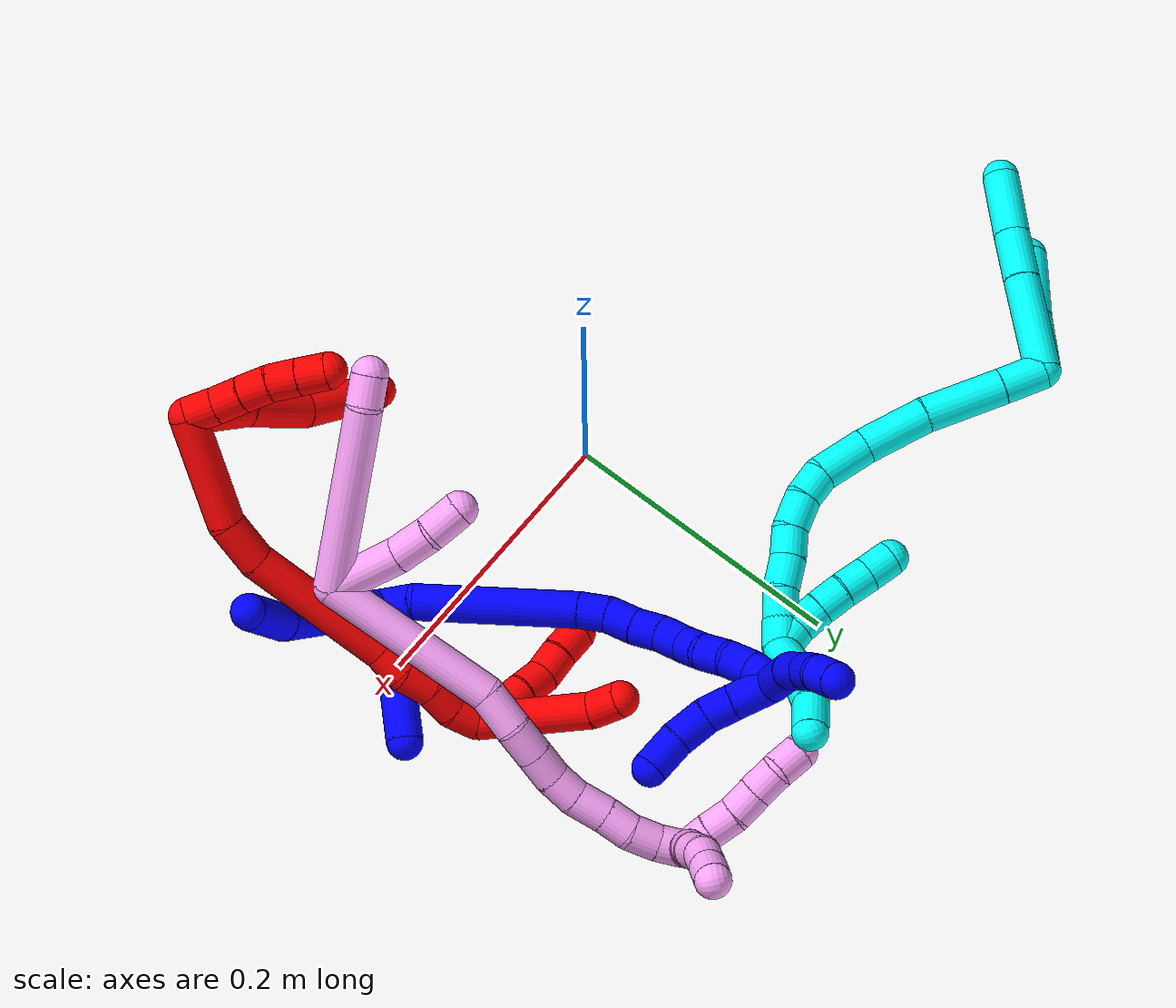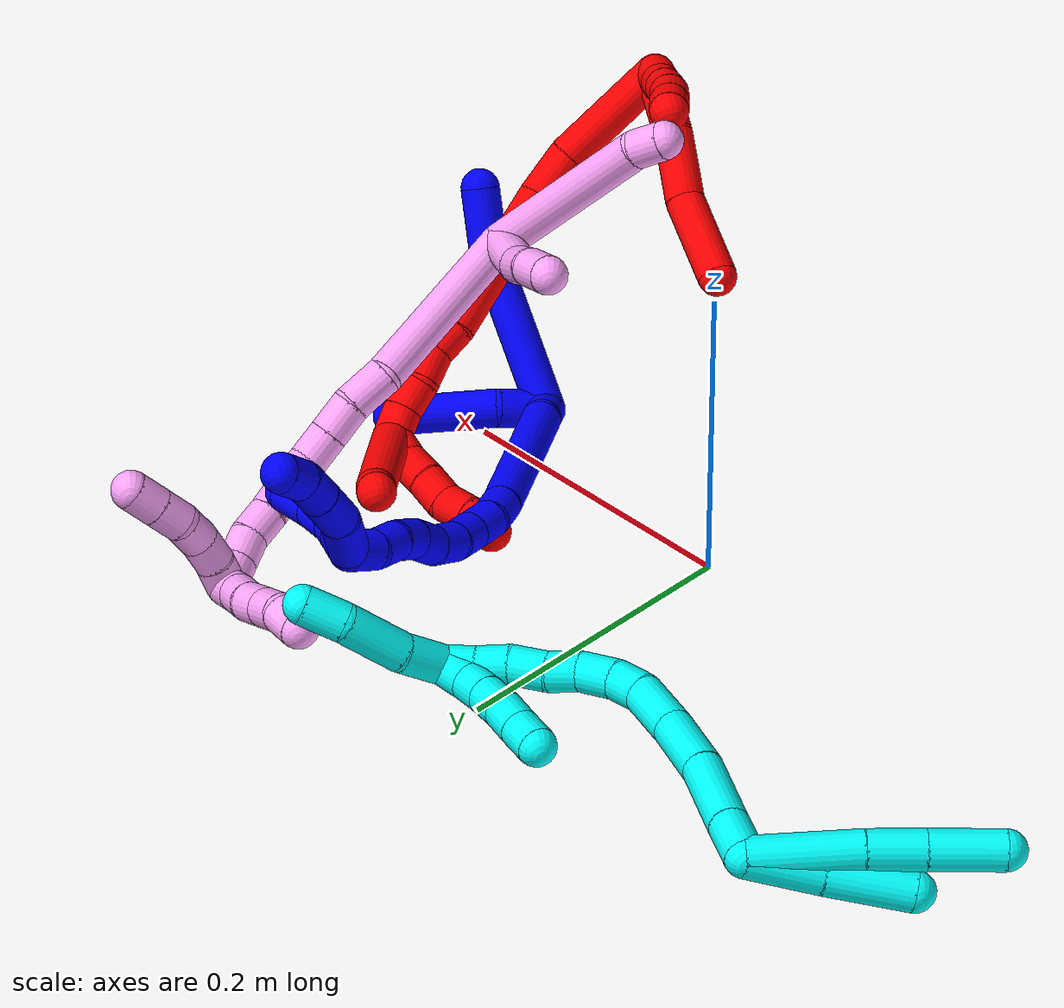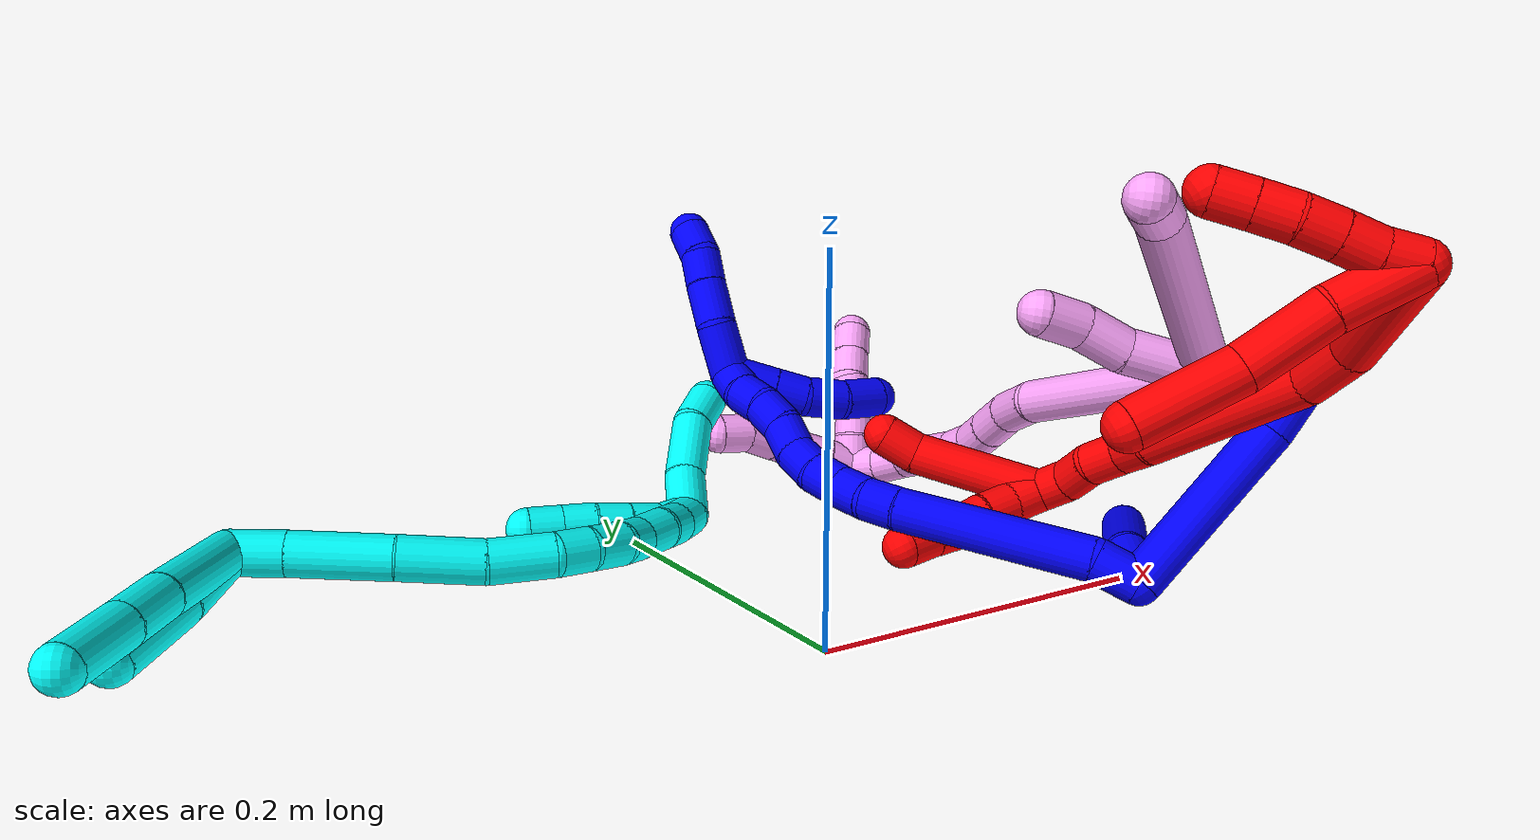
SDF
<sdf version="1.7">
 <world name="default">
  <plugin name="TubeGeneratorPlugin" filename="libtube_generator_plugin.so"/>
  <model name="photoneo_s_sensor">
   <static>1</static>
   <pose>0 0 2 1.57079 1.57079 3.14159</pose>
   <link name="link">
    <inertial><mass>0.1</mass></inertial>
    <sensor name="sensor" type="depth">
     <update_rate>30</update_rate>
     <camera>
      <horizontal_fov>1.22</horizontal_fov>
      <image><width>1920</width><height>1200</height><format>B8G8R8</format></image>
      <clip><near>0.1</near><far>4</far></clip>
      <depth_camera><output>points</output></depth_camera>
     </camera>
     <plugin name="camera_plugin" filename="libgazebo_ros_depth_camera.so">
      <baseline>0.2</baseline>
      <alwaysOn>1</alwaysOn>
      <updateRate>0.0</updateRate>
      <cameraName>camera_ir</cameraName>
      <imageTopicName>/camera/color/image_raw</imageTopicName>
      <cameraInfoTopicName>/camera/color/camera_info</cameraInfoTopicName>
      <depthImageTopicName>/camera/depth/image_raw</depthImageTopicName>
      <depthImageCameraInfoTopicName>/camera/depth/camera_info</depthImageCameraInfoTopicName>
      <pointCloudTopicName>/camera/depth/points</pointCloudTopicName>
      <frameName>fr_optical</frameName>
      <pointCloudCutoff>0.1</pointCloudCutoff>
      <pointCloudCutoffMax>2.0</pointCloudCutoffMax>
      <distortionK1>0</distortionK1>
      <distortionK2>0</distortionK2>
      <distortionK3>0</distortionK3>
      <distortionT1>0</distortionT1>
      <distortionT2>0</distortionT2>
      <CxPrime>0</CxPrime>
      <Cx>0</Cx>
      <Cy>0</Cy>
      <focalLength>0</focalLength>
      <hackBaseline>0</hackBaseline>
     </plugin>
    </sensor>
   </link>
  </model>
  <gravity>0 0 -9.8</gravity>
  <magnetic_field>6e-06 2.3e-05 -4.2e-05</magnetic_field>
  <atmosphere type="adiabatic"/>
  <physics name="default_physics" default="0" type="ode">
   <max_step_size>0.003</max_step_size>
   <real_time_factor>1</real_time_factor>
   <real_time_update_rate>1000</real_time_update_rate>
   <max_contacts>10000</max_contacts>
   <ode>
    <solver>
     <type>quick</type>
     <iters>100</iters>
     <sor>1.3</sor>
     <use_dynamic_moi_rescaling>0</use_dynamic_moi_rescaling>
    </solver>
    <constraints>
     <contact_max_correcting_vel>0</contact_max_correcting_vel>
     <contact_surface_layer>0.001</contact_surface_layer>
     <cfm>0</cfm>
     <erp>0.2</erp>
    </constraints>
   </ode>
  </physics>
  <scene><ambient>0.4 0.4 0.4 1</ambient><background>0.7 0.7 0.7 1</background><shadows>0</shadows></scene>
  <audio><device>default</device></audio>
  <spherical_coordinates>
   <surface_model>EARTH_WGS84</surface_model>
   <latitude_deg>0</latitude_deg>
   <longitude_deg>0</longitude_deg>
   <elevation>0</elevation>
   <heading_deg>0</heading_deg>
  </spherical_coordinates>
  <model name="bin">
   <static>1</static>
   <link name="bottom">
    <collision name="collision-bottom">
     <pose>0 0 -0.01 0 -0 0</pose>
     <geometry><box><size>0.8 0.6 0.02</size></box></geometry>
     <surface>
      <friction><ode><mu>100</mu><mu2>100</mu2></ode></friction>
      <contact><collide_bitmask>65535</collide_bitmask></contact>
     </surface>
    </collision>
   </link>
   <link name="west_wall">
    <collision name="collision-west_wall">
     <pose>-0.41 0 0.1 0 -0 0</pose>
     <geometry><box><size>0.02 0.6 0.2</size></box></geometry>
     <surface>
      <friction><ode><mu>100</mu><mu2>100</mu2></ode></friction>
      <contact><collide_bitmask>65535</collide_bitmask></contact>
     </surface>
    </collision>
   </link>
   <link name="east_wall">
    <collision name="collision-east_wall">
     <pose>0.41 0 0.1 0 -0 0</pose>
     <geometry><box><size>0.02 0.6 0.2</size></box></geometry>
     <surface>
      <friction><ode><mu>100</mu><mu2>100</mu2></ode></friction>
      <contact><collide_bitmask>65535</collide_bitmask></contact>
     </surface>
    </collision>
   </link>
   <link name="south_wall">
    <collision name="collision-south_wall">
     <pose>0 -0.31 0.1 0 -0 0</pose>
     <geometry><box><size>0.8 0.02 0.2</size></box></geometry>
     <surface>
      <friction><ode><mu>100</mu><mu2>100</mu2></ode></friction>
      <contact><collide_bitmask>65535</collide_bitmask></contact>
     </surface>
    </collision>
   </link>
   <link name="north_wall">
    <collision name="collision-north_wall">
     <pose>0 0.31 0.1 0 -0 0</pose>
     <geometry><box><size>0.8 0.02 0.2</size></box></geometry>
     <surface>
      <friction><ode><mu>100</mu><mu2>100</mu2></ode></friction>
      <contact><collide_bitmask>65535</collide_bitmask></contact>
     </surface>
    </collision>
   </link>
  </model>
  <model name="1">
   <static>0</static>
   <link name="1">
    <collision name="collision-cylinder-e_1_2_8">
     <pose>-0.004441 0.00738 0.053213 -0.137812 -0.082482 0.005696</pose>
     <geometry><cylinder><radius>0.0125</radius><length>0.107812</length></cylinder></geometry>
     <surface>
      <friction><ode><mu>1.16</mu><mu2>1.16</mu2><slip1>0</slip1><slip2>0</slip2></ode></friction>
      <contact><ode><kp>1e+06</kp><kd>1</kd><max_vel>0</max_vel><min_depth>0.001</min_depth></ode></contact>
     </surface>
    </collision>
    <visual name="visual-cylinder-e_1_2_8">
     <pose>-0.004441 0.00738 0.053213 -0.137812 -0.082482 0.005696</pose>
     <geometry><cylinder><radius>0.0125</radius><length>0.107812</length></cylinder></geometry>
     <material><ambient>0 0 1 1</ambient></material>
    </visual>
    <collision name="collision-cylinder-e_2_8_6">
     <pose>-0.015144 0.014215 0.126563 0.0271 -0.301369 -0.004115</pose>
     <geometry><cylinder><radius>0.0125</radius><length>0.042188</length></cylinder></geometry>
     <surface>
      <friction><ode><mu>1.16</mu><mu2>1.16</mu2><slip1>0</slip1><slip2>0</slip2></ode></friction>
      <contact><ode><kp>1e+06</kp><kd>1</kd><max_vel>0</max_vel><min_depth>0.001</min_depth></ode></contact>
     </surface>
    </collision>
    <visual name="visual-cylinder-e_2_8_6">
     <pose>-0.015144 0.014215 0.126563 0.0271 -0.301369 -0.004115</pose>
     <geometry><cylinder><radius>0.0125</radius><length>0.042188</length></cylinder></geometry>
     <material><ambient>0 0 1 1</ambient></material>
    </visual>
    <collision name="collision-cylinder-e_1_2_9">
     <pose>-0.000232 0.015767 0.003412 -1.3577 -0.014372 0.011595</pose>
     <geometry><cylinder><radius>0.0125</radius><length>0.032267</length></cylinder></geometry>
     <surface>
      <friction><ode><mu>1.16</mu><mu2>1.16</mu2><slip1>0</slip1><slip2>0</slip2></ode></friction>
      <contact><ode><kp>1e+06</kp><kd>1</kd><max_vel>0</max_vel><min_depth>0.001</min_depth></ode></contact>
     </surface>
    </collision>
    <visual name="visual-cylinder-e_1_2_9">
     <pose>-0.000232 0.015767 0.003412 -1.3577 -0.014372 0.011595</pose>
     <geometry><cylinder><radius>0.0125</radius><length>0.032267</length></cylinder></geometry>
     <material><ambient>0 0 1 1</ambient></material>
    </visual>
    <collision name="collision-cylinder-e_2_9_5">
     <pose>0.009478 0.063395 0.012567 -1.39244 0.29795 -0.249596</pose>
     <geometry><cylinder><radius>0.0125</radius><length>0.067733</length></cylinder></geometry>
     <surface>
      <friction><ode><mu>1.16</mu><mu2>1.16</mu2><slip1>0</slip1><slip2>0</slip2></ode></friction>
      <contact><ode><kp>1e+06</kp><kd>1</kd><max_vel>0</max_vel><min_depth>0.001</min_depth></ode></contact>
     </surface>
    </collision>
    <visual name="visual-cylinder-e_2_9_5">
     <pose>0.009478 0.063395 0.012567 -1.39244 0.29795 -0.249596</pose>
     <geometry><cylinder><radius>0.0125</radius><length>0.067733</length></cylinder></geometry>
     <material><ambient>0 0 1 1</ambient></material>
    </visual>
    <collision name="collision-cylinder-e_1_2_10">
     <pose>-0.010716 0.005351 -0.004548 -2.2753 -0.990679 1.72574</pose>
     <geometry><cylinder><radius>0.0125</radius><length>0.025624</length></cylinder></geometry>
     <surface>
      <friction><ode><mu>1.16</mu><mu2>1.16</mu2><slip1>0</slip1><slip2>0</slip2></ode></friction>
      <contact><ode><kp>1e+06</kp><kd>1</kd><max_vel>0</max_vel><min_depth>0.001</min_depth></ode></contact>
     </surface>
    </collision>
    <visual name="visual-cylinder-e_1_2_10">
     <pose>-0.010716 0.005351 -0.004548 -2.2753 -0.990679 1.72574</pose>
     <geometry><cylinder><radius>0.0125</radius><length>0.025624</length></cylinder></geometry>
     <material><ambient>0 0 1 1</ambient></material>
    </visual>
    <collision name="collision-cylinder-e_2_10_11">
     <pose>-0.057586 0.040776 -0.040206 -2.37311 -0.696041 1.46257</pose>
     <geometry><cylinder><radius>0.0125</radius><length>0.112773</length></cylinder></geometry>
     <surface>
      <friction><ode><mu>1.16</mu><mu2>1.16</mu2><slip1>0</slip1><slip2>0</slip2></ode></friction>
      <contact><ode><kp>1e+06</kp><kd>1</kd><max_vel>0</max_vel><min_depth>0.001</min_depth></ode></contact>
     </surface>
    </collision>
    <visual name="visual-cylinder-e_2_10_11">
     <pose>-0.057586 0.040776 -0.040206 -2.37311 -0.696041 1.46257</pose>
     <geometry><cylinder><radius>0.0125</radius><length>0.112773</length></cylinder></geometry>
     <material><ambient>0 0 1 1</ambient></material>
    </visual>
    <collision name="collision-cylinder-e_3_11_12">
     <pose>-0.099859 0.077293 -0.07635 -2.23403 -0.642464 1.19745</pose>
     <geometry><cylinder><radius>0.0125</radius><length>0.020423</length></cylinder></geometry>
     <surface>
      <friction><ode><mu>1.16</mu><mu2>1.16</mu2><slip1>0</slip1><slip2>0</slip2></ode></friction>
      <contact><ode><kp>1e+06</kp><kd>1</kd><max_vel>0</max_vel><min_depth>0.001</min_depth></ode></contact>
     </surface>
    </collision>
    <visual name="visual-cylinder-e_3_11_12">
     <pose>-0.099859 0.077293 -0.07635 -2.23403 -0.642464 1.19745</pose>
     <geometry><cylinder><radius>0.0125</radius><length>0.020423</length></cylinder></geometry>
     <material><ambient>0 0 1 1</ambient></material>
    </visual>
    <collision name="collision-cylinder-e_4_12_13">
     <pose>-0.110663 0.092024 -0.084923 -1.97443 -0.47944 0.709053</pose>
     <geometry><cylinder><radius>0.0125</radius><length>0.020316</length></cylinder></geometry>
     <surface>
      <friction><ode><mu>1.16</mu><mu2>1.16</mu2><slip1>0</slip1><slip2>0</slip2></ode></friction>
      <contact><ode><kp>1e+06</kp><kd>1</kd><max_vel>0</max_vel><min_depth>0.001</min_depth></ode></contact>
     </surface>
    </collision>
    <visual name="visual-cylinder-e_4_12_13">
     <pose>-0.110663 0.092024 -0.084923 -1.97443 -0.47944 0.709053</pose>
     <geometry><cylinder><radius>0.0125</radius><length>0.020316</length></cylinder></geometry>
     <material><ambient>0 0 1 1</ambient></material>
    </visual>
    <collision name="collision-cylinder-e_5_13_14">
     <pose>-0.121364 0.107762 -0.091656 -1.97575 -0.638447 0.929359</pose>
     <geometry><cylinder><radius>0.0125</radius><length>0.020188</length></cylinder></geometry>
     <surface>
      <friction><ode><mu>1.16</mu><mu2>1.16</mu2><slip1>0</slip1><slip2>0</slip2></ode></friction>
      <contact><ode><kp>1e+06</kp><kd>1</kd><max_vel>0</max_vel><min_depth>0.001</min_depth></ode></contact>
     </surface>
    </collision>
    <visual name="visual-cylinder-e_5_13_14">
     <pose>-0.121364 0.107762 -0.091656 -1.97575 -0.638447 0.929359</pose>
     <geometry><cylinder><radius>0.0125</radius><length>0.020188</length></cylinder></geometry>
     <material><ambient>0 0 1 1</ambient></material>
    </visual>
    <collision name="collision-cylinder-e_6_14_15">
     <pose>-0.133044 0.123802 -0.095812 -1.68234 -0.580187 0.644375</pose>
     <geometry><cylinder><radius>0.0125</radius><length>0.020669</length></cylinder></geometry>
     <surface>
      <friction><ode><mu>1.16</mu><mu2>1.16</mu2><slip1>0</slip1><slip2>0</slip2></ode></friction>
      <contact><ode><kp>1e+06</kp><kd>1</kd><max_vel>0</max_vel><min_depth>0.001</min_depth></ode></contact>
     </surface>
    </collision>
    <visual name="visual-cylinder-e_6_14_15">
     <pose>-0.133044 0.123802 -0.095812 -1.68234 -0.580187 0.644375</pose>
     <geometry><cylinder><radius>0.0125</radius><length>0.020669</length></cylinder></geometry>
     <material><ambient>0 0 1 1</ambient></material>
    </visual>
    <collision name="collision-cylinder-e_7_15_16">
     <pose>-0.145257 0.139673 -0.094731 -1.29729 -0.713591 0.550778</pose>
     <geometry><cylinder><radius>0.0125</radius><length>0.020007</length></cylinder></geometry>
     <surface>
      <friction><ode><mu>1.16</mu><mu2>1.16</mu2><slip1>0</slip1><slip2>0</slip2></ode></friction>
      <contact><ode><kp>1e+06</kp><kd>1</kd><max_vel>0</max_vel><min_depth>0.001</min_depth></ode></contact>
     </surface>
    </collision>
    <visual name="visual-cylinder-e_7_15_16">
     <pose>-0.145257 0.139673 -0.094731 -1.29729 -0.713591 0.550778</pose>
     <geometry><cylinder><radius>0.0125</radius><length>0.020007</length></cylinder></geometry>
     <material><ambient>0 0 1 1</ambient></material>
    </visual>
    <collision name="collision-cylinder-e_8_16_17">
     <pose>-0.15853 0.154328 -0.093328 -1.65733 -0.737532 0.797671</pose>
     <geometry><cylinder><radius>0.0125</radius><length>0.02</length></cylinder></geometry>
     <surface>
      <friction><ode><mu>1.16</mu><mu2>1.16</mu2><slip1>0</slip1><slip2>0</slip2></ode></friction>
      <contact><ode><kp>1e+06</kp><kd>1</kd><max_vel>0</max_vel><min_depth>0.001</min_depth></ode></contact>
     </surface>
    </collision>
    <visual name="visual-cylinder-e_8_16_17">
     <pose>-0.15853 0.154328 -0.093328 -1.65733 -0.737532 0.797671</pose>
     <geometry><cylinder><radius>0.0125</radius><length>0.02</length></cylinder></geometry>
     <material><ambient>0 0 1 1</ambient></material>
    </visual>
    <collision name="collision-cylinder-e_9_17_18">
     <pose>-0.17054 0.169831 -0.096413 -1.86295 -0.556956 0.734232</pose>
     <geometry><cylinder><radius>0.0125</radius><length>0.020001</length></cylinder></geometry>
     <surface>
      <friction><ode><mu>1.16</mu><mu2>1.16</mu2><slip1>0</slip1><slip2>0</slip2></ode></friction>
      <contact><ode><kp>1e+06</kp><kd>1</kd><max_vel>0</max_vel><min_depth>0.001</min_depth></ode></contact>
     </surface>
    </collision>
    <visual name="visual-cylinder-e_9_17_18">
     <pose>-0.17054 0.169831 -0.096413 -1.86295 -0.556956 0.734232</pose>
     <geometry><cylinder><radius>0.0125</radius><length>0.020001</length></cylinder></geometry>
     <material><ambient>0 0 1 1</ambient></material>
    </visual>
    <collision name="collision-cylinder-e_10_18_1">
     <pose>-0.18019 0.186954 -0.098589 -1.54096 -0.451535 0.438689</pose>
     <geometry><cylinder><radius>0.0125</radius><length>0.02</length></cylinder></geometry>
     <surface>
      <friction><ode><mu>1.16</mu><mu2>1.16</mu2><slip1>0</slip1><slip2>0</slip2></ode></friction>
      <contact><ode><kp>1e+06</kp><kd>1</kd><max_vel>0</max_vel><min_depth>0.001</min_depth></ode></contact>
     </surface>
    </collision>
    <visual name="visual-cylinder-e_10_18_1">
     <pose>-0.18019 0.186954 -0.098589 -1.54096 -0.451535 0.438689</pose>
     <geometry><cylinder><radius>0.0125</radius><length>0.02</length></cylinder></geometry>
     <material><ambient>0 0 1 1</ambient></material>
    </visual>
    <collision name="collision-cylinder-e_1_1_19">
     <pose>-0.198555 0.200178 -0.091222 -0.537342 -1.0376 0.311854</pose>
     <geometry><cylinder><radius>0.0125</radius><length>0.032515</length></cylinder></geometry>
     <surface>
      <friction><ode><mu>1.16</mu><mu2>1.16</mu2><slip1>0</slip1><slip2>0</slip2></ode></friction>
      <contact><ode><kp>1e+06</kp><kd>1</kd><max_vel>0</max_vel><min_depth>0.001</min_depth></ode></contact>
     </surface>
    </collision>
    <visual name="visual-cylinder-e_1_1_19">
     <pose>-0.198555 0.200178 -0.091222 -0.537342 -1.0376 0.311854</pose>
     <geometry><cylinder><radius>0.0125</radius><length>0.032515</length></cylinder></geometry>
     <material><ambient>0 0 1 1</ambient></material>
    </visual>
    <collision name="collision-cylinder-e_2_19_20">
     <pose>-0.22265 0.211336 -0.078236 -0.866469 -0.837638 0.406131</pose>
     <geometry><cylinder><radius>0.0125</radius><length>0.02717</length></cylinder></geometry>
     <surface>
      <friction><ode><mu>1.16</mu><mu2>1.16</mu2><slip1>0</slip1><slip2>0</slip2></ode></friction>
      <contact><ode><kp>1e+06</kp><kd>1</kd><max_vel>0</max_vel><min_depth>0.001</min_depth></ode></contact>
     </surface>
    </collision>
    <visual name="visual-cylinder-e_2_19_20">
     <pose>-0.22265 0.211336 -0.078236 -0.866469 -0.837638 0.406131</pose>
     <geometry><cylinder><radius>0.0125</radius><length>0.02717</length></cylinder></geometry>
     <material><ambient>0 0 1 1</ambient></material>
    </visual>
    <collision name="collision-cylinder-e_3_20_21">
     <pose>-0.239788 0.223788 -0.067695 -0.870739 -0.772829 0.374076</pose>
     <geometry><cylinder><radius>0.0125</radius><length>0.020179</length></cylinder></geometry>
     <surface>
      <friction><ode><mu>1.16</mu><mu2>1.16</mu2><slip1>0</slip1><slip2>0</slip2></ode></friction>
      <contact><ode><kp>1e+06</kp><kd>1</kd><max_vel>0</max_vel><min_depth>0.001</min_depth></ode></contact>
     </surface>
    </collision>
    <visual name="visual-cylinder-e_3_20_21">
     <pose>-0.239788 0.223788 -0.067695 -0.870739 -0.772829 0.374076</pose>
     <geometry><cylinder><radius>0.0125</radius><length>0.020179</length></cylinder></geometry>
     <material><ambient>0 0 1 1</ambient></material>
    </visual>
    <collision name="collision-cylinder-e_4_21_4">
     <pose>-0.253292 0.236732 -0.0609 -1.28978 -0.696611 0.533236</pose>
     <geometry><cylinder><radius>0.0125</radius><length>0.020136</length></cylinder></geometry>
     <surface>
      <friction><ode><mu>1.16</mu><mu2>1.16</mu2><slip1>0</slip1><slip2>0</slip2></ode></friction>
      <contact><ode><kp>1e+06</kp><kd>1</kd><max_vel>0</max_vel><min_depth>0.001</min_depth></ode></contact>
     </surface>
    </collision>
    <visual name="visual-cylinder-e_4_21_4">
     <pose>-0.253292 0.236732 -0.0609 -1.28978 -0.696611 0.533236</pose>
     <geometry><cylinder><radius>0.0125</radius><length>0.020136</length></cylinder></geometry>
     <material><ambient>0 0 1 1</ambient></material>
    </visual>
    <collision name="collision-cylinder-e_1_1_22">
     <pose>-0.172381 0.194456 -0.090992 0.200891 1.01981 0.112606</pose>
     <geometry><cylinder><radius>0.0125</radius><length>0.028574</length></cylinder></geometry>
     <surface>
      <friction><ode><mu>1.16</mu><mu2>1.16</mu2><slip1>0</slip1><slip2>0</slip2></ode></friction>
      <contact><ode><kp>1e+06</kp><kd>1</kd><max_vel>0</max_vel><min_depth>0.001</min_depth></ode></contact>
     </surface>
    </collision>
    <visual name="visual-cylinder-e_1_1_22">
     <pose>-0.172381 0.194456 -0.090992 0.200891 1.01981 0.112606</pose>
     <geometry><cylinder><radius>0.0125</radius><length>0.028574</length></cylinder></geometry>
     <material><ambient>0 0 1 1</ambient></material>
    </visual>
    <collision name="collision-cylinder-e_2_22_23">
     <pose>-0.151627 0.192178 -0.078401 0.148186 1.01581 0.082587</pose>
     <geometry><cylinder><radius>0.0125</radius><length>0.020193</length></cylinder></geometry>
     <surface>
      <friction><ode><mu>1.16</mu><mu2>1.16</mu2><slip1>0</slip1><slip2>0</slip2></ode></friction>
      <contact><ode><kp>1e+06</kp><kd>1</kd><max_vel>0</max_vel><min_depth>0.001</min_depth></ode></contact>
     </surface>
    </collision>
    <visual name="visual-cylinder-e_2_22_23">
     <pose>-0.151627 0.192178 -0.078401 0.148186 1.01581 0.082587</pose>
     <geometry><cylinder><radius>0.0125</radius><length>0.020193</length></cylinder></geometry>
     <material><ambient>0 0 1 1</ambient></material>
    </visual>
    <collision name="collision-cylinder-e_3_23_24">
     <pose>-0.133465 0.193772 -0.065585 -0.30527 0.880078 -0.144604</pose>
     <geometry><cylinder><radius>0.0125</radius><length>0.024861</length></cylinder></geometry>
     <surface>
      <friction><ode><mu>1.16</mu><mu2>1.16</mu2><slip1>0</slip1><slip2>0</slip2></ode></friction>
      <contact><ode><kp>1e+06</kp><kd>1</kd><max_vel>0</max_vel><min_depth>0.001</min_depth></ode></contact>
     </surface>
    </collision>
    <visual name="visual-cylinder-e_3_23_24">
     <pose>-0.133465 0.193772 -0.065585 -0.30527 0.880078 -0.144604</pose>
     <geometry><cylinder><radius>0.0125</radius><length>0.024861</length></cylinder></geometry>
     <material><ambient>0 0 1 1</ambient></material>
    </visual>
    <collision name="collision-cylinder-e_4_24_3">
     <pose>-0.115208 0.201282 -0.049529 -0.54283 0.718021 -0.208109</pose>
     <geometry><cylinder><radius>0.0125</radius><length>0.026372</length></cylinder></geometry>
     <surface>
      <friction><ode><mu>1.16</mu><mu2>1.16</mu2><slip1>0</slip1><slip2>0</slip2></ode></friction>
      <contact><ode><kp>1e+06</kp><kd>1</kd><max_vel>0</max_vel><min_depth>0.001</min_depth></ode></contact>
     </surface>
    </collision>
    <visual name="visual-cylinder-e_4_24_3">
     <pose>-0.115208 0.201282 -0.049529 -0.54283 0.718021 -0.208109</pose>
     <geometry><cylinder><radius>0.0125</radius><length>0.026372</length></cylinder></geometry>
     <material><ambient>0 0 1 1</ambient></material>
    </visual>
    <collision name="collision-sphere-3">
     <pose>-0.106533 0.206412 -0.041026 0 -0 0</pose>
     <geometry><sphere><radius>0.0125</radius></sphere></geometry>
     <surface>
      <friction><ode><mu>1.16</mu><mu2>1.16</mu2><slip1>0</slip1><slip2>0</slip2></ode></friction>
      <contact><ode><kp>1e+06</kp><kd>1</kd><max_vel>0</max_vel><min_depth>0.001</min_depth></ode></contact>
     </surface>
    </collision>
    <visual name="visual-sphere-3">
     <pose>-0.106533 0.206412 -0.041026 0 -0 0</pose>
     <geometry><sphere><radius>0.0125</radius></sphere></geometry>
     <material><ambient>0 0 1 1</ambient></material>
    </visual>
    <collision name="collision-sphere-24">
     <pose>-0.123883 0.196152 -0.058032 0 -0 0</pose>
     <geometry><sphere><radius>0.0125</radius></sphere></geometry>
     <surface>
      <friction><ode><mu>1.16</mu><mu2>1.16</mu2><slip1>0</slip1><slip2>0</slip2></ode></friction>
      <contact><ode><kp>1e+06</kp><kd>1</kd><max_vel>0</max_vel><min_depth>0.001</min_depth></ode></contact>
     </surface>
    </collision>
    <visual name="visual-sphere-24">
     <pose>-0.123883 0.196152 -0.058032 0 -0 0</pose>
     <geometry><sphere><radius>0.0125</radius></sphere></geometry>
     <material><ambient>0 0 1 1</ambient></material>
    </visual>
    <collision name="collision-sphere-23">
     <pose>-0.143046 0.191392 -0.073139 0 -0 0</pose>
     <geometry><sphere><radius>0.0125</radius></sphere></geometry>
     <surface>
      <friction><ode><mu>1.16</mu><mu2>1.16</mu2><slip1>0</slip1><slip2>0</slip2></ode></friction>
      <contact><ode><kp>1e+06</kp><kd>1</kd><max_vel>0</max_vel><min_depth>0.001</min_depth></ode></contact>
     </surface>
    </collision>
    <visual name="visual-sphere-23">
     <pose>-0.143046 0.191392 -0.073139 0 -0 0</pose>
     <geometry><sphere><radius>0.0125</radius></sphere></geometry>
     <material><ambient>0 0 1 1</ambient></material>
    </visual>
    <collision name="collision-sphere-22">
     <pose>-0.160208 0.192963 -0.083662 0 -0 0</pose>
     <geometry><sphere><radius>0.0125</radius></sphere></geometry>
     <surface>
      <friction><ode><mu>1.16</mu><mu2>1.16</mu2><slip1>0</slip1><slip2>0</slip2></ode></friction>
      <contact><ode><kp>1e+06</kp><kd>1</kd><max_vel>0</max_vel><min_depth>0.001</min_depth></ode></contact>
     </surface>
    </collision>
    <visual name="visual-sphere-22">
     <pose>-0.160208 0.192963 -0.083662 0 -0 0</pose>
     <geometry><sphere><radius>0.0125</radius></sphere></geometry>
     <material><ambient>0 0 1 1</ambient></material>
    </visual>
    <collision name="collision-sphere-4">
     <pose>-0.259752 0.244152 -0.058758 0 -0 0</pose>
     <geometry><sphere><radius>0.0125</radius></sphere></geometry>
     <surface>
      <friction><ode><mu>1.16</mu><mu2>1.16</mu2><slip1>0</slip1><slip2>0</slip2></ode></friction>
      <contact><ode><kp>1e+06</kp><kd>1</kd><max_vel>0</max_vel><min_depth>0.001</min_depth></ode></contact>
     </surface>
    </collision>
    <visual name="visual-sphere-4">
     <pose>-0.259752 0.244152 -0.058758 0 -0 0</pose>
     <geometry><sphere><radius>0.0125</radius></sphere></geometry>
     <material><ambient>0 0 1 1</ambient></material>
    </visual>
    <collision name="collision-sphere-21">
     <pose>-0.246832 0.229313 -0.063042 0 -0 0</pose>
     <geometry><sphere><radius>0.0125</radius></sphere></geometry>
     <surface>
      <friction><ode><mu>1.16</mu><mu2>1.16</mu2><slip1>0</slip1><slip2>0</slip2></ode></friction>
      <contact><ode><kp>1e+06</kp><kd>1</kd><max_vel>0</max_vel><min_depth>0.001</min_depth></ode></contact>
     </surface>
    </collision>
    <visual name="visual-sphere-21">
     <pose>-0.246832 0.229313 -0.063042 0 -0 0</pose>
     <geometry><sphere><radius>0.0125</radius></sphere></geometry>
     <material><ambient>0 0 1 1</ambient></material>
    </visual>
    <collision name="collision-sphere-20">
     <pose>-0.232744 0.218264 -0.072349 0 -0 0</pose>
     <geometry><sphere><radius>0.0125</radius></sphere></geometry>
     <surface>
      <friction><ode><mu>1.16</mu><mu2>1.16</mu2><slip1>0</slip1><slip2>0</slip2></ode></friction>
      <contact><ode><kp>1e+06</kp><kd>1</kd><max_vel>0</max_vel><min_depth>0.001</min_depth></ode></contact>
     </surface>
    </collision>
    <visual name="visual-sphere-20">
     <pose>-0.232744 0.218264 -0.072349 0 -0 0</pose>
     <geometry><sphere><radius>0.0125</radius></sphere></geometry>
     <material><ambient>0 0 1 1</ambient></material>
    </visual>
    <collision name="collision-sphere-10">
     <pose>-0.021432 0.010701 -0.009096 0 -0 0</pose>
     <geometry><sphere><radius>0.0125</radius></sphere></geometry>
     <surface>
      <friction><ode><mu>1.16</mu><mu2>1.16</mu2><slip1>0</slip1><slip2>0</slip2></ode></friction>
      <contact><ode><kp>1e+06</kp><kd>1</kd><max_vel>0</max_vel><min_depth>0.001</min_depth></ode></contact>
     </surface>
    </collision>
    <visual name="visual-sphere-10">
     <pose>-0.021432 0.010701 -0.009096 0 -0 0</pose>
     <geometry><sphere><radius>0.0125</radius></sphere></geometry>
     <material><ambient>0 0 1 1</ambient></material>
    </visual>
    <collision name="collision-sphere-5">
     <pose>0.01942 0.095255 0.01831 0 -0 0</pose>
     <geometry><sphere><radius>0.0125</radius></sphere></geometry>
     <surface>
      <friction><ode><mu>1.16</mu><mu2>1.16</mu2><slip1>0</slip1><slip2>0</slip2></ode></friction>
      <contact><ode><kp>1e+06</kp><kd>1</kd><max_vel>0</max_vel><min_depth>0.001</min_depth></ode></contact>
     </surface>
    </collision>
    <visual name="visual-sphere-5">
     <pose>0.01942 0.095255 0.01831 0 -0 0</pose>
     <geometry><sphere><radius>0.0125</radius></sphere></geometry>
     <material><ambient>0 0 1 1</ambient></material>
    </visual>
    <collision name="collision-sphere-6">
     <pose>-0.021405 0.013669 0.146699 0 -0 0</pose>
     <geometry><sphere><radius>0.0125</radius></sphere></geometry>
     <surface>
      <friction><ode><mu>1.16</mu><mu2>1.16</mu2><slip1>0</slip1><slip2>0</slip2></ode></friction>
      <contact><ode><kp>1e+06</kp><kd>1</kd><max_vel>0</max_vel><min_depth>0.001</min_depth></ode></contact>
     </surface>
    </collision>
    <visual name="visual-sphere-6">
     <pose>-0.021405 0.013669 0.146699 0 -0 0</pose>
     <geometry><sphere><radius>0.0125</radius></sphere></geometry>
     <material><ambient>0 0 1 1</ambient></material>
    </visual>
    <collision name="collision-sphere-9">
     <pose>-0.000464 0.031534 0.006823 0 -0 0</pose>
     <geometry><sphere><radius>0.0125</radius></sphere></geometry>
     <surface>
      <friction><ode><mu>1.16</mu><mu2>1.16</mu2><slip1>0</slip1><slip2>0</slip2></ode></friction>
      <contact><ode><kp>1e+06</kp><kd>1</kd><max_vel>0</max_vel><min_depth>0.001</min_depth></ode></contact>
     </surface>
    </collision>
    <visual name="visual-sphere-9">
     <pose>-0.000464 0.031534 0.006823 0 -0 0</pose>
     <geometry><sphere><radius>0.0125</radius></sphere></geometry>
     <material><ambient>0 0 1 1</ambient></material>
    </visual>
    <collision name="collision-sphere-2">
     <geometry><sphere><radius>0.0125</radius></sphere></geometry>
     <surface>
      <friction><ode><mu>1.16</mu><mu2>1.16</mu2><slip1>0</slip1><slip2>0</slip2></ode></friction>
      <contact><ode><kp>1e+06</kp><kd>1</kd><max_vel>0</max_vel><min_depth>0.001</min_depth></ode></contact>
     </surface>
    </collision>
    <visual name="visual-sphere-2">
     <geometry><sphere><radius>0.0125</radius></sphere></geometry>
     <material><ambient>0 0 1 1</ambient></material>
    </visual>
    <collision name="collision-sphere-19">
     <pose>-0.212555 0.204408 -0.084123 0 -0 0</pose>
     <geometry><sphere><radius>0.0125</radius></sphere></geometry>
     <surface>
      <friction><ode><mu>1.16</mu><mu2>1.16</mu2><slip1>0</slip1><slip2>0</slip2></ode></friction>
      <contact><ode><kp>1e+06</kp><kd>1</kd><max_vel>0</max_vel><min_depth>0.001</min_depth></ode></contact>
     </surface>
    </collision>
    <visual name="visual-sphere-19">
     <pose>-0.212555 0.204408 -0.084123 0 -0 0</pose>
     <geometry><sphere><radius>0.0125</radius></sphere></geometry>
     <material><ambient>0 0 1 1</ambient></material>
    </visual>
    <collision name="collision-sphere-8">
     <pose>-0.008883 0.01476 0.106427 0 -0 0</pose>
     <geometry><sphere><radius>0.0125</radius></sphere></geometry>
     <surface>
      <friction><ode><mu>1.16</mu><mu2>1.16</mu2><slip1>0</slip1><slip2>0</slip2></ode></friction>
      <contact><ode><kp>1e+06</kp><kd>1</kd><max_vel>0</max_vel><min_depth>0.001</min_depth></ode></contact>
     </surface>
    </collision>
    <visual name="visual-sphere-8">
     <pose>-0.008883 0.01476 0.106427 0 -0 0</pose>
     <geometry><sphere><radius>0.0125</radius></sphere></geometry>
     <material><ambient>0 0 1 1</ambient></material>
    </visual>
    <collision name="collision-sphere-11">
     <pose>-0.09374 0.070851 -0.071316 0 -0 0</pose>
     <geometry><sphere><radius>0.0125</radius></sphere></geometry>
     <surface>
      <friction><ode><mu>1.16</mu><mu2>1.16</mu2><slip1>0</slip1><slip2>0</slip2></ode></friction>
      <contact><ode><kp>1e+06</kp><kd>1</kd><max_vel>0</max_vel><min_depth>0.001</min_depth></ode></contact>
     </surface>
    </collision>
    <visual name="visual-sphere-11">
     <pose>-0.09374 0.070851 -0.071316 0 -0 0</pose>
     <geometry><sphere><radius>0.0125</radius></sphere></geometry>
     <material><ambient>0 0 1 1</ambient></material>
    </visual>
    <collision name="collision-sphere-12">
     <pose>-0.105977 0.083735 -0.081383 0 -0 0</pose>
     <geometry><sphere><radius>0.0125</radius></sphere></geometry>
     <surface>
      <friction><ode><mu>1.16</mu><mu2>1.16</mu2><slip1>0</slip1><slip2>0</slip2></ode></friction>
      <contact><ode><kp>1e+06</kp><kd>1</kd><max_vel>0</max_vel><min_depth>0.001</min_depth></ode></contact>
     </surface>
    </collision>
    <visual name="visual-sphere-12">
     <pose>-0.105977 0.083735 -0.081383 0 -0 0</pose>
     <geometry><sphere><radius>0.0125</radius></sphere></geometry>
     <material><ambient>0 0 1 1</ambient></material>
    </visual>
    <collision name="collision-sphere-13">
     <pose>-0.115348 0.100312 -0.088463 0 -0 0</pose>
     <geometry><sphere><radius>0.0125</radius></sphere></geometry>
     <surface>
      <friction><ode><mu>1.16</mu><mu2>1.16</mu2><slip1>0</slip1><slip2>0</slip2></ode></friction>
      <contact><ode><kp>1e+06</kp><kd>1</kd><max_vel>0</max_vel><min_depth>0.001</min_depth></ode></contact>
     </surface>
    </collision>
    <visual name="visual-sphere-13">
     <pose>-0.115348 0.100312 -0.088463 0 -0 0</pose>
     <geometry><sphere><radius>0.0125</radius></sphere></geometry>
     <material><ambient>0 0 1 1</ambient></material>
    </visual>
    <collision name="collision-sphere-14">
     <pose>-0.127379 0.115212 -0.09485 0 -0 0</pose>
     <geometry><sphere><radius>0.0125</radius></sphere></geometry>
     <surface>
      <friction><ode><mu>1.16</mu><mu2>1.16</mu2><slip1>0</slip1><slip2>0</slip2></ode></friction>
      <contact><ode><kp>1e+06</kp><kd>1</kd><max_vel>0</max_vel><min_depth>0.001</min_depth></ode></contact>
     </surface>
    </collision>
    <visual name="visual-sphere-14">
     <pose>-0.127379 0.115212 -0.09485 0 -0 0</pose>
     <geometry><sphere><radius>0.0125</radius></sphere></geometry>
     <material><ambient>0 0 1 1</ambient></material>
    </visual>
    <collision name="collision-sphere-15">
     <pose>-0.138709 0.132391 -0.096774 0 -0 0</pose>
     <geometry><sphere><radius>0.0125</radius></sphere></geometry>
     <surface>
      <friction><ode><mu>1.16</mu><mu2>1.16</mu2><slip1>0</slip1><slip2>0</slip2></ode></friction>
      <contact><ode><kp>1e+06</kp><kd>1</kd><max_vel>0</max_vel><min_depth>0.001</min_depth></ode></contact>
     </surface>
    </collision>
    <visual name="visual-sphere-15">
     <pose>-0.138709 0.132391 -0.096774 0 -0 0</pose>
     <geometry><sphere><radius>0.0125</radius></sphere></geometry>
     <material><ambient>0 0 1 1</ambient></material>
    </visual>
    <collision name="collision-sphere-16">
     <pose>-0.151805 0.146955 -0.092688 0 -0 0</pose>
     <geometry><sphere><radius>0.0125</radius></sphere></geometry>
     <surface>
      <friction><ode><mu>1.16</mu><mu2>1.16</mu2><slip1>0</slip1><slip2>0</slip2></ode></friction>
      <contact><ode><kp>1e+06</kp><kd>1</kd><max_vel>0</max_vel><min_depth>0.001</min_depth></ode></contact>
     </surface>
    </collision>
    <visual name="visual-sphere-16">
     <pose>-0.151805 0.146955 -0.092688 0 -0 0</pose>
     <geometry><sphere><radius>0.0125</radius></sphere></geometry>
     <material><ambient>0 0 1 1</ambient></material>
    </visual>
    <collision name="collision-sphere-17">
     <pose>-0.165254 0.161702 -0.093968 0 -0 0</pose>
     <geometry><sphere><radius>0.0125</radius></sphere></geometry>
     <surface>
      <friction><ode><mu>1.16</mu><mu2>1.16</mu2><slip1>0</slip1><slip2>0</slip2></ode></friction>
      <contact><ode><kp>1e+06</kp><kd>1</kd><max_vel>0</max_vel><min_depth>0.001</min_depth></ode></contact>
     </surface>
    </collision>
    <visual name="visual-sphere-17">
     <pose>-0.165254 0.161702 -0.093968 0 -0 0</pose>
     <geometry><sphere><radius>0.0125</radius></sphere></geometry>
     <material><ambient>0 0 1 1</ambient></material>
    </visual>
    <collision name="collision-sphere-18">
     <pose>-0.175827 0.17796 -0.098858 0 -0 0</pose>
     <geometry><sphere><radius>0.0125</radius></sphere></geometry>
     <surface>
      <friction><ode><mu>1.16</mu><mu2>1.16</mu2><slip1>0</slip1><slip2>0</slip2></ode></friction>
      <contact><ode><kp>1e+06</kp><kd>1</kd><max_vel>0</max_vel><min_depth>0.001</min_depth></ode></contact>
     </surface>
    </collision>
    <visual name="visual-sphere-18">
     <pose>-0.175827 0.17796 -0.098858 0 -0 0</pose>
     <geometry><sphere><radius>0.0125</radius></sphere></geometry>
     <material><ambient>0 0 1 1</ambient></material>
    </visual>
    <collision name="collision-sphere-1">
     <pose>-0.184554 0.195948 -0.098321 0 -0 0</pose>
     <geometry><sphere><radius>0.0125</radius></sphere></geometry>
     <surface>
      <friction><ode><mu>1.16</mu><mu2>1.16</mu2><slip1>0</slip1><slip2>0</slip2></ode></friction>
      <contact><ode><kp>1e+06</kp><kd>1</kd><max_vel>0</max_vel><min_depth>0.001</min_depth></ode></contact>
     </surface>
    </collision>
    <visual name="visual-sphere-1">
     <pose>-0.184554 0.195948 -0.098321 0 -0 0</pose>
     <geometry><sphere><radius>0.0125</radius></sphere></geometry>
     <material><ambient>0 0 1 1</ambient></material>
    </visual>
    <inertial>
     <pose>-0.088825 0.097638 -0.029592 0 -0 0</pose>
     <mass>0.75</mass>
     <inertia>
      <ixx>0.000258</ixx>
      <ixy>0</ixy>
      <ixz>0</ixz>
      <iyy>0.000317</iyy>
      <iyz>0</iyz>
      <izz>-2.3e-05</izz>
     </inertia>
    </inertial>
   </link>
   <pose>0.178942 -0.034336 0.011701 0.035162 0.840524 -0.409448</pose>
  </model>
  <model name="2">
   <static>0</static>
   <link name="2">
    <collision name="collision-cylinder-e_1_2_8">
     <pose>-0.000176 6.6e-05 -0.022686 -3.1387 -0.007743 2.42687</pose>
     <geometry><cylinder><radius>0.0125</radius><length>0.045374</length></cylinder></geometry>
     <surface>
      <friction><ode><mu>1.16</mu><mu2>1.16</mu2><slip1>0</slip1><slip2>0</slip2></ode></friction>
      <contact><ode><kp>1e+06</kp><kd>1</kd><max_vel>0</max_vel><min_depth>0.001</min_depth></ode></contact>
     </surface>
    </collision>
    <visual name="visual-cylinder-e_1_2_8">
     <pose>-0.000176 6.6e-05 -0.022686 -3.1387 -0.007743 2.42687</pose>
     <geometry><cylinder><radius>0.0125</radius><length>0.045374</length></cylinder></geometry>
     <material><ambient>1 0 0 1</ambient></material>
    </visual>
    <collision name="collision-cylinder-e_2_8_9">
     <pose>0.000243 0.00427 -0.068212 -2.96234 0.025583 -0.282789</pose>
     <geometry><cylinder><radius>0.0125</radius><length>0.046439</length></cylinder></geometry>
     <surface>
      <friction><ode><mu>1.16</mu><mu2>1.16</mu2><slip1>0</slip1><slip2>0</slip2></ode></friction>
      <contact><ode><kp>1e+06</kp><kd>1</kd><max_vel>0</max_vel><min_depth>0.001</min_depth></ode></contact>
     </surface>
    </collision>
    <visual name="visual-cylinder-e_2_8_9">
     <pose>0.000243 0.00427 -0.068212 -2.96234 0.025583 -0.282789</pose>
     <geometry><cylinder><radius>0.0125</radius><length>0.046439</length></cylinder></geometry>
     <material><ambient>1 0 0 1</ambient></material>
    </visual>
    <collision name="collision-cylinder-e_3_9_6">
     <pose>0.002739 0.006447 -0.120017 3.07397 0.065442 1.53797</pose>
     <geometry><cylinder><radius>0.0125</radius><length>0.058188</length></cylinder></geometry>
     <surface>
      <friction><ode><mu>1.16</mu><mu2>1.16</mu2><slip1>0</slip1><slip2>0</slip2></ode></friction>
      <contact><ode><kp>1e+06</kp><kd>1</kd><max_vel>0</max_vel><min_depth>0.001</min_depth></ode></contact>
     </surface>
    </collision>
    <visual name="visual-cylinder-e_3_9_6">
     <pose>0.002739 0.006447 -0.120017 3.07397 0.065442 1.53797</pose>
     <geometry><cylinder><radius>0.0125</radius><length>0.058188</length></cylinder></geometry>
     <material><ambient>1 0 0 1</ambient></material>
    </visual>
    <collision name="collision-cylinder-e_1_2_10">
     <pose>-0.004323 -0.005039 -0.007478 2.54862 -0.447001 -1.27936</pose>
     <geometry><cylinder><radius>0.0125</radius><length>0.02</length></cylinder></geometry>
     <surface>
      <friction><ode><mu>1.16</mu><mu2>1.16</mu2><slip1>0</slip1><slip2>0</slip2></ode></friction>
      <contact><ode><kp>1e+06</kp><kd>1</kd><max_vel>0</max_vel><min_depth>0.001</min_depth></ode></contact>
     </surface>
    </collision>
    <visual name="visual-cylinder-e_1_2_10">
     <pose>-0.004323 -0.005039 -0.007478 2.54862 -0.447001 -1.27936</pose>
     <geometry><cylinder><radius>0.0125</radius><length>0.02</length></cylinder></geometry>
     <material><ambient>1 0 0 1</ambient></material>
    </visual>
    <collision name="collision-cylinder-e_2_10_11">
     <pose>-0.013597 -0.016018 -0.021296 2.38877 -0.518051 -1.18116</pose>
     <geometry><cylinder><radius>0.0125</radius><length>0.02</length></cylinder></geometry>
     <surface>
      <friction><ode><mu>1.16</mu><mu2>1.16</mu2><slip1>0</slip1><slip2>0</slip2></ode></friction>
      <contact><ode><kp>1e+06</kp><kd>1</kd><max_vel>0</max_vel><min_depth>0.001</min_depth></ode></contact>
     </surface>
    </collision>
    <visual name="visual-cylinder-e_2_10_11">
     <pose>-0.013597 -0.016018 -0.021296 2.38877 -0.518051 -1.18116</pose>
     <geometry><cylinder><radius>0.0125</radius><length>0.02</length></cylinder></geometry>
     <material><ambient>1 0 0 1</ambient></material>
    </visual>
    <collision name="collision-cylinder-e_3_11_12">
     <pose>-0.023379 -0.027667 -0.034275 2.43142 -0.504126 -1.21411</pose>
     <geometry><cylinder><radius>0.0125</radius><length>0.02</length></cylinder></geometry>
     <surface>
      <friction><ode><mu>1.16</mu><mu2>1.16</mu2><slip1>0</slip1><slip2>0</slip2></ode></friction>
      <contact><ode><kp>1e+06</kp><kd>1</kd><max_vel>0</max_vel><min_depth>0.001</min_depth></ode></contact>
     </surface>
    </collision>
    <visual name="visual-cylinder-e_3_11_12">
     <pose>-0.023379 -0.027667 -0.034275 2.43142 -0.504126 -1.21411</pose>
     <geometry><cylinder><radius>0.0125</radius><length>0.02</length></cylinder></geometry>
     <material><ambient>1 0 0 1</ambient></material>
    </visual>
    <collision name="collision-cylinder-e_4_12_13">
     <pose>-0.033949 -0.037791 -0.047811 2.57214 -0.611335 -1.646</pose>
     <geometry><cylinder><radius>0.0125</radius><length>0.02</length></cylinder></geometry>
     <surface>
      <friction><ode><mu>1.16</mu><mu2>1.16</mu2><slip1>0</slip1><slip2>0</slip2></ode></friction>
      <contact><ode><kp>1e+06</kp><kd>1</kd><max_vel>0</max_vel><min_depth>0.001</min_depth></ode></contact>
     </surface>
    </collision>
    <visual name="visual-cylinder-e_4_12_13">
     <pose>-0.033949 -0.037791 -0.047811 2.57214 -0.611335 -1.646</pose>
     <geometry><cylinder><radius>0.0125</radius><length>0.02</length></cylinder></geometry>
     <material><ambient>1 0 0 1</ambient></material>
    </visual>
    <collision name="collision-cylinder-e_5_13_5">
     <pose>-0.045408 -0.04642 -0.061746 2.60205 -0.608833 -1.69817</pose>
     <geometry><cylinder><radius>0.0125</radius><length>0.02</length></cylinder></geometry>
     <surface>
      <friction><ode><mu>1.16</mu><mu2>1.16</mu2><slip1>0</slip1><slip2>0</slip2></ode></friction>
      <contact><ode><kp>1e+06</kp><kd>1</kd><max_vel>0</max_vel><min_depth>0.001</min_depth></ode></contact>
     </surface>
    </collision>
    <visual name="visual-cylinder-e_5_13_5">
     <pose>-0.045408 -0.04642 -0.061746 2.60205 -0.608833 -1.69817</pose>
     <geometry><cylinder><radius>0.0125</radius><length>0.02</length></cylinder></geometry>
     <material><ambient>1 0 0 1</ambient></material>
    </visual>
    <collision name="collision-cylinder-e_1_2_14">
     <pose>-0.01419 0.034035 -0.011916 -1.90757 -0.374897 0.522523</pose>
     <geometry><cylinder><radius>0.0125</radius><length>0.077504</length></cylinder></geometry>
     <surface>
      <friction><ode><mu>1.16</mu><mu2>1.16</mu2><slip1>0</slip1><slip2>0</slip2></ode></friction>
      <contact><ode><kp>1e+06</kp><kd>1</kd><max_vel>0</max_vel><min_depth>0.001</min_depth></ode></contact>
     </surface>
    </collision>
    <visual name="visual-cylinder-e_1_2_14">
     <pose>-0.01419 0.034035 -0.011916 -1.90757 -0.374897 0.522523</pose>
     <geometry><cylinder><radius>0.0125</radius><length>0.077504</length></cylinder></geometry>
     <material><ambient>1 0 0 1</ambient></material>
    </visual>
    <collision name="collision-cylinder-e_2_14_15">
     <pose>-0.03524 0.080024 -0.033467 -2.24912 -0.420183 0.838564</pose>
     <geometry><cylinder><radius>0.0125</radius><length>0.033634</length></cylinder></geometry>
     <surface>
      <friction><ode><mu>1.16</mu><mu2>1.16</mu2><slip1>0</slip1><slip2>0</slip2></ode></friction>
      <contact><ode><kp>1e+06</kp><kd>1</kd><max_vel>0</max_vel><min_depth>0.001</min_depth></ode></contact>
     </surface>
    </collision>
    <visual name="visual-cylinder-e_2_14_15">
     <pose>-0.03524 0.080024 -0.033467 -2.24912 -0.420183 0.838564</pose>
     <geometry><cylinder><radius>0.0125</radius><length>0.033634</length></cylinder></geometry>
     <material><ambient>1 0 0 1</ambient></material>
    </visual>
    <collision name="collision-cylinder-e_3_15_16">
     <pose>-0.067892 0.117674 -0.080021 -2.5336 -0.520624 1.40785</pose>
     <geometry><cylinder><radius>0.0125</radius><length>0.103701</length></cylinder></geometry>
     <surface>
      <friction><ode><mu>1.16</mu><mu2>1.16</mu2><slip1>0</slip1><slip2>0</slip2></ode></friction>
      <contact><ode><kp>1e+06</kp><kd>1</kd><max_vel>0</max_vel><min_depth>0.001</min_depth></ode></contact>
     </surface>
    </collision>
    <visual name="visual-cylinder-e_3_15_16">
     <pose>-0.067892 0.117674 -0.080021 -2.5336 -0.520624 1.40785</pose>
     <geometry><cylinder><radius>0.0125</radius><length>0.103701</length></cylinder></geometry>
     <material><ambient>1 0 0 1</ambient></material>
    </visual>
    <collision name="collision-cylinder-e_4_16_17">
     <pose>-0.10001 0.149501 -0.122982 -2.34863 -0.633755 1.32895</pose>
     <geometry><cylinder><radius>0.0125</radius><length>0.021367</length></cylinder></geometry>
     <surface>
      <friction><ode><mu>1.16</mu><mu2>1.16</mu2><slip1>0</slip1><slip2>0</slip2></ode></friction>
      <contact><ode><kp>1e+06</kp><kd>1</kd><max_vel>0</max_vel><min_depth>0.001</min_depth></ode></contact>
     </surface>
    </collision>
    <visual name="visual-cylinder-e_4_16_17">
     <pose>-0.10001 0.149501 -0.122982 -2.34863 -0.633755 1.32895</pose>
     <geometry><cylinder><radius>0.0125</radius><length>0.021367</length></cylinder></geometry>
     <material><ambient>1 0 0 1</ambient></material>
    </visual>
    <collision name="collision-cylinder-e_5_17_18">
     <pose>-0.111338 0.160152 -0.138011 -2.67576 -0.461436 1.56096</pose>
     <geometry><cylinder><radius>0.0125</radius><length>0.022468</length></cylinder></geometry>
     <surface>
      <friction><ode><mu>1.16</mu><mu2>1.16</mu2><slip1>0</slip1><slip2>0</slip2></ode></friction>
      <contact><ode><kp>1e+06</kp><kd>1</kd><max_vel>0</max_vel><min_depth>0.001</min_depth></ode></contact>
     </surface>
    </collision>
    <visual name="visual-cylinder-e_5_17_18">
     <pose>-0.111338 0.160152 -0.138011 -2.67576 -0.461436 1.56096</pose>
     <geometry><cylinder><radius>0.0125</radius><length>0.022468</length></cylinder></geometry>
     <material><ambient>1 0 0 1</ambient></material>
    </visual>
    <collision name="collision-cylinder-e_6_18_19">
     <pose>-0.120409 0.171607 -0.153858 -2.35067 -0.395138 0.894277</pose>
     <geometry><cylinder><radius>0.0125</radius><length>0.02114</length></cylinder></geometry>
     <surface>
      <friction><ode><mu>1.16</mu><mu2>1.16</mu2><slip1>0</slip1><slip2>0</slip2></ode></friction>
      <contact><ode><kp>1e+06</kp><kd>1</kd><max_vel>0</max_vel><min_depth>0.001</min_depth></ode></contact>
     </surface>
    </collision>
    <visual name="visual-cylinder-e_6_18_19">
     <pose>-0.120409 0.171607 -0.153858 -2.35067 -0.395138 0.894277</pose>
     <geometry><cylinder><radius>0.0125</radius><length>0.02114</length></cylinder></geometry>
     <material><ambient>1 0 0 1</ambient></material>
    </visual>
    <collision name="collision-cylinder-e_7_19_1">
     <pose>-0.12862 0.18224 -0.169147 -2.72821 -0.422896 1.59423</pose>
     <geometry><cylinder><radius>0.0125</radius><length>0.020186</length></cylinder></geometry>
     <surface>
      <friction><ode><mu>1.16</mu><mu2>1.16</mu2><slip1>0</slip1><slip2>0</slip2></ode></friction>
      <contact><ode><kp>1e+06</kp><kd>1</kd><max_vel>0</max_vel><min_depth>0.001</min_depth></ode></contact>
     </surface>
    </collision>
    <visual name="visual-cylinder-e_7_19_1">
     <pose>-0.12862 0.18224 -0.169147 -2.72821 -0.422896 1.59423</pose>
     <geometry><cylinder><radius>0.0125</radius><length>0.020186</length></cylinder></geometry>
     <material><ambient>1 0 0 1</ambient></material>
    </visual>
    <collision name="collision-cylinder-e_1_1_20">
     <pose>-0.156574 0.172673 -0.20535 2.69606 -0.658455 -1.97065</pose>
     <geometry><cylinder><radius>0.0125</radius><length>0.07783</length></cylinder></geometry>
     <surface>
      <friction><ode><mu>1.16</mu><mu2>1.16</mu2><slip1>0</slip1><slip2>0</slip2></ode></friction>
      <contact><ode><kp>1e+06</kp><kd>1</kd><max_vel>0</max_vel><min_depth>0.001</min_depth></ode></contact>
     </surface>
    </collision>
    <visual name="visual-cylinder-e_1_1_20">
     <pose>-0.156574 0.172673 -0.20535 2.69606 -0.658455 -1.97065</pose>
     <geometry><cylinder><radius>0.0125</radius><length>0.07783</length></cylinder></geometry>
     <material><ambient>1 0 0 1</ambient></material>
    </visual>
    <collision name="collision-cylinder-e_2_20_4">
     <pose>-0.186719 0.152509 -0.239054 2.28064 -0.608093 -1.19887</pose>
     <geometry><cylinder><radius>0.0125</radius><length>0.02217</length></cylinder></geometry>
     <surface>
      <friction><ode><mu>1.16</mu><mu2>1.16</mu2><slip1>0</slip1><slip2>0</slip2></ode></friction>
      <contact><ode><kp>1e+06</kp><kd>1</kd><max_vel>0</max_vel><min_depth>0.001</min_depth></ode></contact>
     </surface>
    </collision>
    <visual name="visual-cylinder-e_2_20_4">
     <pose>-0.186719 0.152509 -0.239054 2.28064 -0.608093 -1.19887</pose>
     <geometry><cylinder><radius>0.0125</radius><length>0.02217</length></cylinder></geometry>
     <material><ambient>1 0 0 1</ambient></material>
    </visual>
    <collision name="collision-cylinder-e_1_1_21">
     <pose>-0.131473 0.183311 -0.187138 2.87357 0.129255 0.895095</pose>
     <geometry><cylinder><radius>0.0125</radius><length>0.02</length></cylinder></geometry>
     <surface>
      <friction><ode><mu>1.16</mu><mu2>1.16</mu2><slip1>0</slip1><slip2>0</slip2></ode></friction>
      <contact><ode><kp>1e+06</kp><kd>1</kd><max_vel>0</max_vel><min_depth>0.001</min_depth></ode></contact>
     </surface>
    </collision>
    <visual name="visual-cylinder-e_1_1_21">
     <pose>-0.131473 0.183311 -0.187138 2.87357 0.129255 0.895095</pose>
     <geometry><cylinder><radius>0.0125</radius><length>0.02</length></cylinder></geometry>
     <material><ambient>1 0 0 1</ambient></material>
    </visual>
    <collision name="collision-cylinder-e_2_21_22">
     <pose>-0.127859 0.176941 -0.205677 2.74636 0.23461 1.06393</pose>
     <geometry><cylinder><radius>0.0125</radius><length>0.02</length></cylinder></geometry>
     <surface>
      <friction><ode><mu>1.16</mu><mu2>1.16</mu2><slip1>0</slip1><slip2>0</slip2></ode></friction>
      <contact><ode><kp>1e+06</kp><kd>1</kd><max_vel>0</max_vel><min_depth>0.001</min_depth></ode></contact>
     </surface>
    </collision>
    <visual name="visual-cylinder-e_2_21_22">
     <pose>-0.127859 0.176941 -0.205677 2.74636 0.23461 1.06393</pose>
     <geometry><cylinder><radius>0.0125</radius><length>0.02</length></cylinder></geometry>
     <material><ambient>1 0 0 1</ambient></material>
    </visual>
    <collision name="collision-cylinder-e_3_22_23">
     <pose>-0.122916 0.170356 -0.223877 2.84293 0.264977 1.44983</pose>
     <geometry><cylinder><radius>0.0125</radius><length>0.02</length></cylinder></geometry>
     <surface>
      <friction><ode><mu>1.16</mu><mu2>1.16</mu2><slip1>0</slip1><slip2>0</slip2></ode></friction>
      <contact><ode><kp>1e+06</kp><kd>1</kd><max_vel>0</max_vel><min_depth>0.001</min_depth></ode></contact>
     </surface>
    </collision>
    <visual name="visual-cylinder-e_3_22_23">
     <pose>-0.122916 0.170356 -0.223877 2.84293 0.264977 1.44983</pose>
     <geometry><cylinder><radius>0.0125</radius><length>0.02</length></cylinder></geometry>
     <material><ambient>1 0 0 1</ambient></material>
    </visual>
    <collision name="collision-cylinder-e_4_23_24">
     <pose>-0.117226 0.161817 -0.240722 2.49946 0.312121 0.883797</pose>
     <geometry><cylinder><radius>0.0125</radius><length>0.02</length></cylinder></geometry>
     <surface>
      <friction><ode><mu>1.16</mu><mu2>1.16</mu2><slip1>0</slip1><slip2>0</slip2></ode></friction>
      <contact><ode><kp>1e+06</kp><kd>1</kd><max_vel>0</max_vel><min_depth>0.001</min_depth></ode></contact>
     </surface>
    </collision>
    <visual name="visual-cylinder-e_4_23_24">
     <pose>-0.117226 0.161817 -0.240722 2.49946 0.312121 0.883797</pose>
     <geometry><cylinder><radius>0.0125</radius><length>0.02</length></cylinder></geometry>
     <material><ambient>1 0 0 1</ambient></material>
    </visual>
    <collision name="collision-cylinder-e_5_24_3">
     <pose>-0.111154 0.151346 -0.256603 2.61781 0.304805 1.04066</pose>
     <geometry><cylinder><radius>0.0125</radius><length>0.02</length></cylinder></geometry>
     <surface>
      <friction><ode><mu>1.16</mu><mu2>1.16</mu2><slip1>0</slip1><slip2>0</slip2></ode></friction>
      <contact><ode><kp>1e+06</kp><kd>1</kd><max_vel>0</max_vel><min_depth>0.001</min_depth></ode></contact>
     </surface>
    </collision>
    <visual name="visual-cylinder-e_5_24_3">
     <pose>-0.111154 0.151346 -0.256603 2.61781 0.304805 1.04066</pose>
     <geometry><cylinder><radius>0.0125</radius><length>0.02</length></cylinder></geometry>
     <material><ambient>1 0 0 1</ambient></material>
    </visual>
    <collision name="collision-sphere-3">
     <pose>-0.108153 0.146575 -0.264864 0 -0 0</pose>
     <geometry><sphere><radius>0.0125</radius></sphere></geometry>
     <surface>
      <friction><ode><mu>1.16</mu><mu2>1.16</mu2><slip1>0</slip1><slip2>0</slip2></ode></friction>
      <contact><ode><kp>1e+06</kp><kd>1</kd><max_vel>0</max_vel><min_depth>0.001</min_depth></ode></contact>
     </surface>
    </collision>
    <visual name="visual-sphere-3">
     <pose>-0.108153 0.146575 -0.264864 0 -0 0</pose>
     <geometry><sphere><radius>0.0125</radius></sphere></geometry>
     <material><ambient>1 0 0 1</ambient></material>
    </visual>
    <collision name="collision-sphere-24">
     <pose>-0.114155 0.156117 -0.248343 0 -0 0</pose>
     <geometry><sphere><radius>0.0125</radius></sphere></geometry>
     <surface>
      <friction><ode><mu>1.16</mu><mu2>1.16</mu2><slip1>0</slip1><slip2>0</slip2></ode></friction>
      <contact><ode><kp>1e+06</kp><kd>1</kd><max_vel>0</max_vel><min_depth>0.001</min_depth></ode></contact>
     </surface>
    </collision>
    <visual name="visual-sphere-24">
     <pose>-0.114155 0.156117 -0.248343 0 -0 0</pose>
     <geometry><sphere><radius>0.0125</radius></sphere></geometry>
     <material><ambient>1 0 0 1</ambient></material>
    </visual>
    <collision name="collision-sphere-23">
     <pose>-0.120297 0.167516 -0.233101 0 -0 0</pose>
     <geometry><sphere><radius>0.0125</radius></sphere></geometry>
     <surface>
      <friction><ode><mu>1.16</mu><mu2>1.16</mu2><slip1>0</slip1><slip2>0</slip2></ode></friction>
      <contact><ode><kp>1e+06</kp><kd>1</kd><max_vel>0</max_vel><min_depth>0.001</min_depth></ode></contact>
     </surface>
    </collision>
    <visual name="visual-sphere-23">
     <pose>-0.120297 0.167516 -0.233101 0 -0 0</pose>
     <geometry><sphere><radius>0.0125</radius></sphere></geometry>
     <material><ambient>1 0 0 1</ambient></material>
    </visual>
    <collision name="collision-sphere-22">
     <pose>-0.125535 0.173196 -0.214653 0 -0 0</pose>
     <geometry><sphere><radius>0.0125</radius></sphere></geometry>
     <surface>
      <friction><ode><mu>1.16</mu><mu2>1.16</mu2><slip1>0</slip1><slip2>0</slip2></ode></friction>
      <contact><ode><kp>1e+06</kp><kd>1</kd><max_vel>0</max_vel><min_depth>0.001</min_depth></ode></contact>
     </surface>
    </collision>
    <visual name="visual-sphere-22">
     <pose>-0.125535 0.173196 -0.214653 0 -0 0</pose>
     <geometry><sphere><radius>0.0125</radius></sphere></geometry>
     <material><ambient>1 0 0 1</ambient></material>
    </visual>
    <collision name="collision-sphere-21">
     <pose>-0.130184 0.180685 -0.196701 0 -0 0</pose>
     <geometry><sphere><radius>0.0125</radius></sphere></geometry>
     <surface>
      <friction><ode><mu>1.16</mu><mu2>1.16</mu2><slip1>0</slip1><slip2>0</slip2></ode></friction>
      <contact><ode><kp>1e+06</kp><kd>1</kd><max_vel>0</max_vel><min_depth>0.001</min_depth></ode></contact>
     </surface>
    </collision>
    <visual name="visual-sphere-21">
     <pose>-0.130184 0.180685 -0.196701 0 -0 0</pose>
     <geometry><sphere><radius>0.0125</radius></sphere></geometry>
     <material><ambient>1 0 0 1</ambient></material>
    </visual>
    <collision name="collision-sphere-4">
     <pose>-0.193052 0.145609 -0.244983 0 -0 0</pose>
     <geometry><sphere><radius>0.0125</radius></sphere></geometry>
     <surface>
      <friction><ode><mu>1.16</mu><mu2>1.16</mu2><slip1>0</slip1><slip2>0</slip2></ode></friction>
      <contact><ode><kp>1e+06</kp><kd>1</kd><max_vel>0</max_vel><min_depth>0.001</min_depth></ode></contact>
     </surface>
    </collision>
    <visual name="visual-sphere-4">
     <pose>-0.193052 0.145609 -0.244983 0 -0 0</pose>
     <geometry><sphere><radius>0.0125</radius></sphere></geometry>
     <material><ambient>1 0 0 1</ambient></material>
    </visual>
    <collision name="collision-sphere-20">
     <pose>-0.180386 0.159409 -0.233125 0 -0 0</pose>
     <geometry><sphere><radius>0.0125</radius></sphere></geometry>
     <surface>
      <friction><ode><mu>1.16</mu><mu2>1.16</mu2><slip1>0</slip1><slip2>0</slip2></ode></friction>
      <contact><ode><kp>1e+06</kp><kd>1</kd><max_vel>0</max_vel><min_depth>0.001</min_depth></ode></contact>
     </surface>
    </collision>
    <visual name="visual-sphere-20">
     <pose>-0.180386 0.159409 -0.233125 0 -0 0</pose>
     <geometry><sphere><radius>0.0125</radius></sphere></geometry>
     <material><ambient>1 0 0 1</ambient></material>
    </visual>
    <collision name="collision-sphere-11">
     <pose>-0.018549 -0.021958 -0.027636 0 -0 0</pose>
     <geometry><sphere><radius>0.0125</radius></sphere></geometry>
     <surface>
      <friction><ode><mu>1.16</mu><mu2>1.16</mu2><slip1>0</slip1><slip2>0</slip2></ode></friction>
      <contact><ode><kp>1e+06</kp><kd>1</kd><max_vel>0</max_vel><min_depth>0.001</min_depth></ode></contact>
     </surface>
    </collision>
    <visual name="visual-sphere-11">
     <pose>-0.018549 -0.021958 -0.027636 0 -0 0</pose>
     <geometry><sphere><radius>0.0125</radius></sphere></geometry>
     <material><ambient>1 0 0 1</ambient></material>
    </visual>
    <collision name="collision-sphere-10">
     <pose>-0.008645 -0.010078 -0.014956 0 -0 0</pose>
     <geometry><sphere><radius>0.0125</radius></sphere></geometry>
     <surface>
      <friction><ode><mu>1.16</mu><mu2>1.16</mu2><slip1>0</slip1><slip2>0</slip2></ode></friction>
      <contact><ode><kp>1e+06</kp><kd>1</kd><max_vel>0</max_vel><min_depth>0.001</min_depth></ode></contact>
     </surface>
    </collision>
    <visual name="visual-sphere-10">
     <pose>-0.008645 -0.010078 -0.014956 0 -0 0</pose>
     <geometry><sphere><radius>0.0125</radius></sphere></geometry>
     <material><ambient>1 0 0 1</ambient></material>
    </visual>
    <collision name="collision-sphere-6">
     <pose>0.004642 0.004485 -0.148982 0 -0 0</pose>
     <geometry><sphere><radius>0.0125</radius></sphere></geometry>
     <surface>
      <friction><ode><mu>1.16</mu><mu2>1.16</mu2><slip1>0</slip1><slip2>0</slip2></ode></friction>
      <contact><ode><kp>1e+06</kp><kd>1</kd><max_vel>0</max_vel><min_depth>0.001</min_depth></ode></contact>
     </surface>
    </collision>
    <visual name="visual-sphere-6">
     <pose>0.004642 0.004485 -0.148982 0 -0 0</pose>
     <geometry><sphere><radius>0.0125</radius></sphere></geometry>
     <material><ambient>1 0 0 1</ambient></material>
    </visual>
    <collision name="collision-sphere-9">
     <pose>0.000837 0.008408 -0.091052 0 -0 0</pose>
     <geometry><sphere><radius>0.0125</radius></sphere></geometry>
     <surface>
      <friction><ode><mu>1.16</mu><mu2>1.16</mu2><slip1>0</slip1><slip2>0</slip2></ode></friction>
      <contact><ode><kp>1e+06</kp><kd>1</kd><max_vel>0</max_vel><min_depth>0.001</min_depth></ode></contact>
     </surface>
    </collision>
    <visual name="visual-sphere-9">
     <pose>0.000837 0.008408 -0.091052 0 -0 0</pose>
     <geometry><sphere><radius>0.0125</radius></sphere></geometry>
     <material><ambient>1 0 0 1</ambient></material>
    </visual>
    <collision name="collision-sphere-2">
     <geometry><sphere><radius>0.0125</radius></sphere></geometry>
     <surface>
      <friction><ode><mu>1.16</mu><mu2>1.16</mu2><slip1>0</slip1><slip2>0</slip2></ode></friction>
      <contact><ode><kp>1e+06</kp><kd>1</kd><max_vel>0</max_vel><min_depth>0.001</min_depth></ode></contact>
     </surface>
    </collision>
    <visual name="visual-sphere-2">
     <geometry><sphere><radius>0.0125</radius></sphere></geometry>
     <material><ambient>1 0 0 1</ambient></material>
    </visual>
    <collision name="collision-sphere-19">
     <pose>-0.124477 0.178543 -0.160718 0 -0 0</pose>
     <geometry><sphere><radius>0.0125</radius></sphere></geometry>
     <surface>
      <friction><ode><mu>1.16</mu><mu2>1.16</mu2><slip1>0</slip1><slip2>0</slip2></ode></friction>
      <contact><ode><kp>1e+06</kp><kd>1</kd><max_vel>0</max_vel><min_depth>0.001</min_depth></ode></contact>
     </surface>
    </collision>
    <visual name="visual-sphere-19">
     <pose>-0.124477 0.178543 -0.160718 0 -0 0</pose>
     <geometry><sphere><radius>0.0125</radius></sphere></geometry>
     <material><ambient>1 0 0 1</ambient></material>
    </visual>
    <collision name="collision-sphere-8">
     <pose>-0.000351 0.000131 -0.045372 0 -0 0</pose>
     <geometry><sphere><radius>0.0125</radius></sphere></geometry>
     <surface>
      <friction><ode><mu>1.16</mu><mu2>1.16</mu2><slip1>0</slip1><slip2>0</slip2></ode></friction>
      <contact><ode><kp>1e+06</kp><kd>1</kd><max_vel>0</max_vel><min_depth>0.001</min_depth></ode></contact>
     </surface>
    </collision>
    <visual name="visual-sphere-8">
     <pose>-0.000351 0.000131 -0.045372 0 -0 0</pose>
     <geometry><sphere><radius>0.0125</radius></sphere></geometry>
     <material><ambient>1 0 0 1</ambient></material>
    </visual>
    <collision name="collision-sphere-12">
     <pose>-0.02821 -0.033375 -0.040915 0 -0 0</pose>
     <geometry><sphere><radius>0.0125</radius></sphere></geometry>
     <surface>
      <friction><ode><mu>1.16</mu><mu2>1.16</mu2><slip1>0</slip1><slip2>0</slip2></ode></friction>
      <contact><ode><kp>1e+06</kp><kd>1</kd><max_vel>0</max_vel><min_depth>0.001</min_depth></ode></contact>
     </surface>
    </collision>
    <visual name="visual-sphere-12">
     <pose>-0.02821 -0.033375 -0.040915 0 -0 0</pose>
     <geometry><sphere><radius>0.0125</radius></sphere></geometry>
     <material><ambient>1 0 0 1</ambient></material>
    </visual>
    <collision name="collision-sphere-13">
     <pose>-0.039689 -0.042206 -0.054708 0 -0 0</pose>
     <geometry><sphere><radius>0.0125</radius></sphere></geometry>
     <surface>
      <friction><ode><mu>1.16</mu><mu2>1.16</mu2><slip1>0</slip1><slip2>0</slip2></ode></friction>
      <contact><ode><kp>1e+06</kp><kd>1</kd><max_vel>0</max_vel><min_depth>0.001</min_depth></ode></contact>
     </surface>
    </collision>
    <visual name="visual-sphere-13">
     <pose>-0.039689 -0.042206 -0.054708 0 -0 0</pose>
     <geometry><sphere><radius>0.0125</radius></sphere></geometry>
     <material><ambient>1 0 0 1</ambient></material>
    </visual>
    <collision name="collision-sphere-5">
     <pose>-0.051127 -0.050634 -0.068784 0 -0 0</pose>
     <geometry><sphere><radius>0.0125</radius></sphere></geometry>
     <surface>
      <friction><ode><mu>1.16</mu><mu2>1.16</mu2><slip1>0</slip1><slip2>0</slip2></ode></friction>
      <contact><ode><kp>1e+06</kp><kd>1</kd><max_vel>0</max_vel><min_depth>0.001</min_depth></ode></contact>
     </surface>
    </collision>
    <visual name="visual-sphere-5">
     <pose>-0.051127 -0.050634 -0.068784 0 -0 0</pose>
     <geometry><sphere><radius>0.0125</radius></sphere></geometry>
     <material><ambient>1 0 0 1</ambient></material>
    </visual>
    <collision name="collision-sphere-14">
     <pose>-0.02838 0.068069 -0.023832 0 -0 0</pose>
     <geometry><sphere><radius>0.0125</radius></sphere></geometry>
     <surface>
      <friction><ode><mu>1.16</mu><mu2>1.16</mu2><slip1>0</slip1><slip2>0</slip2></ode></friction>
      <contact><ode><kp>1e+06</kp><kd>1</kd><max_vel>0</max_vel><min_depth>0.001</min_depth></ode></contact>
     </surface>
    </collision>
    <visual name="visual-sphere-14">
     <pose>-0.02838 0.068069 -0.023832 0 -0 0</pose>
     <geometry><sphere><radius>0.0125</radius></sphere></geometry>
     <material><ambient>1 0 0 1</ambient></material>
    </visual>
    <collision name="collision-sphere-15">
     <pose>-0.0421 0.091979 -0.043101 0 -0 0</pose>
     <geometry><sphere><radius>0.0125</radius></sphere></geometry>
     <surface>
      <friction><ode><mu>1.16</mu><mu2>1.16</mu2><slip1>0</slip1><slip2>0</slip2></ode></friction>
      <contact><ode><kp>1e+06</kp><kd>1</kd><max_vel>0</max_vel><min_depth>0.001</min_depth></ode></contact>
     </surface>
    </collision>
    <visual name="visual-sphere-15">
     <pose>-0.0421 0.091979 -0.043101 0 -0 0</pose>
     <geometry><sphere><radius>0.0125</radius></sphere></geometry>
     <material><ambient>1 0 0 1</ambient></material>
    </visual>
    <collision name="collision-sphere-16">
     <pose>-0.093683 0.143368 -0.116941 0 -0 0</pose>
     <geometry><sphere><radius>0.0125</radius></sphere></geometry>
     <surface>
      <friction><ode><mu>1.16</mu><mu2>1.16</mu2><slip1>0</slip1><slip2>0</slip2></ode></friction>
      <contact><ode><kp>1e+06</kp><kd>1</kd><max_vel>0</max_vel><min_depth>0.001</min_depth></ode></contact>
     </surface>
    </collision>
    <visual name="visual-sphere-16">
     <pose>-0.093683 0.143368 -0.116941 0 -0 0</pose>
     <geometry><sphere><radius>0.0125</radius></sphere></geometry>
     <material><ambient>1 0 0 1</ambient></material>
    </visual>
    <collision name="collision-sphere-17">
     <pose>-0.106336 0.155634 -0.129023 0 -0 0</pose>
     <geometry><sphere><radius>0.0125</radius></sphere></geometry>
     <surface>
      <friction><ode><mu>1.16</mu><mu2>1.16</mu2><slip1>0</slip1><slip2>0</slip2></ode></friction>
      <contact><ode><kp>1e+06</kp><kd>1</kd><max_vel>0</max_vel><min_depth>0.001</min_depth></ode></contact>
     </surface>
    </collision>
    <visual name="visual-sphere-17">
     <pose>-0.106336 0.155634 -0.129023 0 -0 0</pose>
     <geometry><sphere><radius>0.0125</radius></sphere></geometry>
     <material><ambient>1 0 0 1</ambient></material>
    </visual>
    <collision name="collision-sphere-18">
     <pose>-0.11634 0.16467 -0.146998 0 -0 0</pose>
     <geometry><sphere><radius>0.0125</radius></sphere></geometry>
     <surface>
      <friction><ode><mu>1.16</mu><mu2>1.16</mu2><slip1>0</slip1><slip2>0</slip2></ode></friction>
      <contact><ode><kp>1e+06</kp><kd>1</kd><max_vel>0</max_vel><min_depth>0.001</min_depth></ode></contact>
     </surface>
    </collision>
    <visual name="visual-sphere-18">
     <pose>-0.11634 0.16467 -0.146998 0 -0 0</pose>
     <geometry><sphere><radius>0.0125</radius></sphere></geometry>
     <material><ambient>1 0 0 1</ambient></material>
    </visual>
    <collision name="collision-sphere-1">
     <pose>-0.132762 0.185938 -0.177576 0 -0 0</pose>
     <geometry><sphere><radius>0.0125</radius></sphere></geometry>
     <surface>
      <friction><ode><mu>1.16</mu><mu2>1.16</mu2><slip1>0</slip1><slip2>0</slip2></ode></friction>
      <contact><ode><kp>1e+06</kp><kd>1</kd><max_vel>0</max_vel><min_depth>0.001</min_depth></ode></contact>
     </surface>
    </collision>
    <visual name="visual-sphere-1">
     <pose>-0.132762 0.185938 -0.177576 0 -0 0</pose>
     <geometry><sphere><radius>0.0125</radius></sphere></geometry>
     <material><ambient>1 0 0 1</ambient></material>
    </visual>
    <inertial>
     <pose>-0.066526 0.084326 -0.107918 0 -0 0</pose>
     <mass>0.75</mass>
     <inertia>
      <ixx>0.00013</ixx>
      <ixy>0</ixy>
      <ixz>0</ixz>
      <iyy>0.000136</iyy>
      <iyz>0</iyz>
      <izz>-1.7e-05</izz>
     </inertia>
    </inertial>
   </link>
   <pose>0.209548 -0.162786 0.196065 -1.04957 0.457559 -1.8219</pose>
  </model>
  <model name="3">
   <static>0</static>
   <link name="3">
    <collision name="collision-cylinder-e_1_2_8">
     <pose>-0.033401 0.000325 0.008189 -0.039662 -1.33019 0.031108</pose>
     <geometry><cylinder><radius>0.0125</radius><length>0.068784</length></cylinder></geometry>
     <surface>
      <friction><ode><mu>1.16</mu><mu2>1.16</mu2><slip1>0</slip1><slip2>0</slip2></ode></friction>
      <contact><ode><kp>1e+06</kp><kd>1</kd><max_vel>0</max_vel><min_depth>0.001</min_depth></ode></contact>
     </surface>
    </collision>
    <visual name="visual-cylinder-e_1_2_8">
     <pose>-0.033401 0.000325 0.008189 -0.039662 -1.33019 0.031108</pose>
     <geometry><cylinder><radius>0.0125</radius><length>0.068784</length></cylinder></geometry>
     <material><ambient>0.003922 1 0.996078 1</ambient></material>
    </visual>
    <collision name="collision-cylinder-e_2_8_9">
     <pose>-0.08378 0.001734 0.020875 -0.236601 -1.30478 0.181111</pose>
     <geometry><cylinder><radius>0.0125</radius><length>0.035192</length></cylinder></geometry>
     <surface>
      <friction><ode><mu>1.16</mu><mu2>1.16</mu2><slip1>0</slip1><slip2>0</slip2></ode></friction>
      <contact><ode><kp>1e+06</kp><kd>1</kd><max_vel>0</max_vel><min_depth>0.001</min_depth></ode></contact>
     </surface>
    </collision>
    <visual name="visual-cylinder-e_2_8_9">
     <pose>-0.08378 0.001734 0.020875 -0.236601 -1.30478 0.181111</pose>
     <geometry><cylinder><radius>0.0125</radius><length>0.035192</length></cylinder></geometry>
     <material><ambient>0.003922 1 0.996078 1</ambient></material>
    </visual>
    <collision name="collision-cylinder-e_3_9_6">
     <pose>-0.122837 0.004261 0.03169 -0.224516 -1.28531 0.168402</pose>
     <geometry><cylinder><radius>0.0125</radius><length>0.046024</length></cylinder></geometry>
     <surface>
      <friction><ode><mu>1.16</mu><mu2>1.16</mu2><slip1>0</slip1><slip2>0</slip2></ode></friction>
      <contact><ode><kp>1e+06</kp><kd>1</kd><max_vel>0</max_vel><min_depth>0.001</min_depth></ode></contact>
     </surface>
    </collision>
    <visual name="visual-cylinder-e_3_9_6">
     <pose>-0.122837 0.004261 0.03169 -0.224516 -1.28531 0.168402</pose>
     <geometry><cylinder><radius>0.0125</radius><length>0.046024</length></cylinder></geometry>
     <material><ambient>0.003922 1 0.996078 1</ambient></material>
    </visual>
    <collision name="collision-cylinder-e_1_2_10">
     <pose>-0.02119 0.006629 0.007134 -0.748784 -1.14 0.493445</pose>
     <geometry><cylinder><radius>0.0125</radius><length>0.046641</length></cylinder></geometry>
     <surface>
      <friction><ode><mu>1.16</mu><mu2>1.16</mu2><slip1>0</slip1><slip2>0</slip2></ode></friction>
      <contact><ode><kp>1e+06</kp><kd>1</kd><max_vel>0</max_vel><min_depth>0.001</min_depth></ode></contact>
     </surface>
    </collision>
    <visual name="visual-cylinder-e_1_2_10">
     <pose>-0.02119 0.006629 0.007134 -0.748784 -1.14 0.493445</pose>
     <geometry><cylinder><radius>0.0125</radius><length>0.046641</length></cylinder></geometry>
     <material><ambient>0.003922 1 0.996078 1</ambient></material>
    </visual>
    <collision name="collision-cylinder-e_2_10_5">
     <pose>-0.066585 0.018726 0.024065 -0.508926 -1.13675 0.329234</pose>
     <geometry><cylinder><radius>0.0125</radius><length>0.053359</length></cylinder></geometry>
     <surface>
      <friction><ode><mu>1.16</mu><mu2>1.16</mu2><slip1>0</slip1><slip2>0</slip2></ode></friction>
      <contact><ode><kp>1e+06</kp><kd>1</kd><max_vel>0</max_vel><min_depth>0.001</min_depth></ode></contact>
     </surface>
    </collision>
    <visual name="visual-cylinder-e_2_10_5">
     <pose>-0.066585 0.018726 0.024065 -0.508926 -1.13675 0.329234</pose>
     <geometry><cylinder><radius>0.0125</radius><length>0.053359</length></cylinder></geometry>
     <material><ambient>0.003922 1 0.996078 1</ambient></material>
    </visual>
    <collision name="collision-cylinder-e_1_2_11">
     <pose>-0.000525 4.1e-05 -0.015185 -3.13889 -0.034579 2.98575</pose>
     <geometry><cylinder><radius>0.0125</radius><length>0.030388</length></cylinder></geometry>
     <surface>
      <friction><ode><mu>1.16</mu><mu2>1.16</mu2><slip1>0</slip1><slip2>0</slip2></ode></friction>
      <contact><ode><kp>1e+06</kp><kd>1</kd><max_vel>0</max_vel><min_depth>0.001</min_depth></ode></contact>
     </surface>
    </collision>
    <visual name="visual-cylinder-e_1_2_11">
     <pose>-0.000525 4.1e-05 -0.015185 -3.13889 -0.034579 2.98575</pose>
     <geometry><cylinder><radius>0.0125</radius><length>0.030388</length></cylinder></geometry>
     <material><ambient>0.003922 1 0.996078 1</ambient></material>
    </visual>
    <collision name="collision-cylinder-e_2_11_12">
     <pose>-0.002764 0.000649 -0.058359 -3.12133 -0.061112 2.50146</pose>
     <geometry><cylinder><radius>0.0125</radius><length>0.056095</length></cylinder></geometry>
     <surface>
      <friction><ode><mu>1.16</mu><mu2>1.16</mu2><slip1>0</slip1><slip2>0</slip2></ode></friction>
      <contact><ode><kp>1e+06</kp><kd>1</kd><max_vel>0</max_vel><min_depth>0.001</min_depth></ode></contact>
     </surface>
    </collision>
    <visual name="visual-cylinder-e_2_11_12">
     <pose>-0.002764 0.000649 -0.058359 -3.12133 -0.061112 2.50146</pose>
     <geometry><cylinder><radius>0.0125</radius><length>0.056095</length></cylinder></geometry>
     <material><ambient>0.003922 1 0.996078 1</ambient></material>
    </visual>
    <collision name="collision-cylinder-e_3_12_13">
     <pose>-0.003238 0.002746 -0.109667 -3.07608 0.052964 -1.35957</pose>
     <geometry><cylinder><radius>0.0125</radius><length>0.046804</length></cylinder></geometry>
     <surface>
      <friction><ode><mu>1.16</mu><mu2>1.16</mu2><slip1>0</slip1><slip2>0</slip2></ode></friction>
      <contact><ode><kp>1e+06</kp><kd>1</kd><max_vel>0</max_vel><min_depth>0.001</min_depth></ode></contact>
     </surface>
    </collision>
    <visual name="visual-cylinder-e_3_12_13">
     <pose>-0.003238 0.002746 -0.109667 -3.07608 0.052964 -1.35957</pose>
     <geometry><cylinder><radius>0.0125</radius><length>0.046804</length></cylinder></geometry>
     <material><ambient>0.003922 1 0.996078 1</ambient></material>
    </visual>
    <collision name="collision-cylinder-e_4_13_14">
     <pose>0.001404 0.003326 -0.15093 3.08866 0.187142 2.59169</pose>
     <geometry><cylinder><radius>0.0125</radius><length>0.036577</length></cylinder></geometry>
     <surface>
      <friction><ode><mu>1.16</mu><mu2>1.16</mu2><slip1>0</slip1><slip2>0</slip2></ode></friction>
      <contact><ode><kp>1e+06</kp><kd>1</kd><max_vel>0</max_vel><min_depth>0.001</min_depth></ode></contact>
     </surface>
    </collision>
    <visual name="visual-cylinder-e_4_13_14">
     <pose>0.001404 0.003326 -0.15093 3.08866 0.187142 2.59169</pose>
     <geometry><cylinder><radius>0.0125</radius><length>0.036577</length></cylinder></geometry>
     <material><ambient>0.003922 1 0.996078 1</ambient></material>
    </visual>
    <collision name="collision-cylinder-e_5_14_15">
     <pose>0.010021 0.002395 -0.177858 -3.1393 0.525902 -3.13306</pose>
     <geometry><cylinder><radius>0.0125</radius><length>0.020775</length></cylinder></geometry>
     <surface>
      <friction><ode><mu>1.16</mu><mu2>1.16</mu2><slip1>0</slip1><slip2>0</slip2></ode></friction>
      <contact><ode><kp>1e+06</kp><kd>1</kd><max_vel>0</max_vel><min_depth>0.001</min_depth></ode></contact>
     </surface>
    </collision>
    <visual name="visual-cylinder-e_5_14_15">
     <pose>0.010021 0.002395 -0.177858 -3.1393 0.525902 -3.13306</pose>
     <geometry><cylinder><radius>0.0125</radius><length>0.020775</length></cylinder></geometry>
     <material><ambient>0.003922 1 0.996078 1</ambient></material>
    </visual>
    <collision name="collision-cylinder-e_6_15_16">
     <pose>0.023443 0.003439 -0.195432 -3.02306 0.759079 -2.84625</pose>
     <geometry><cylinder><radius>0.0125</radius><length>0.02385</length></cylinder></geometry>
     <surface>
      <friction><ode><mu>1.16</mu><mu2>1.16</mu2><slip1>0</slip1><slip2>0</slip2></ode></friction>
      <contact><ode><kp>1e+06</kp><kd>1</kd><max_vel>0</max_vel><min_depth>0.001</min_depth></ode></contact>
     </surface>
    </collision>
    <visual name="visual-cylinder-e_6_15_16">
     <pose>0.023443 0.003439 -0.195432 -3.02306 0.759079 -2.84625</pose>
     <geometry><cylinder><radius>0.0125</radius><length>0.02385</length></cylinder></geometry>
     <material><ambient>0.003922 1 0.996078 1</ambient></material>
    </visual>
    <collision name="collision-cylinder-e_7_16_17">
     <pose>0.040608 0.005762 -0.208985 -2.88545 1.05073 -2.70441</pose>
     <geometry><cylinder><radius>0.0125</radius><length>0.020645</length></cylinder></geometry>
     <surface>
      <friction><ode><mu>1.16</mu><mu2>1.16</mu2><slip1>0</slip1><slip2>0</slip2></ode></friction>
      <contact><ode><kp>1e+06</kp><kd>1</kd><max_vel>0</max_vel><min_depth>0.001</min_depth></ode></contact>
     </surface>
    </collision>
    <visual name="visual-cylinder-e_7_16_17">
     <pose>0.040608 0.005762 -0.208985 -2.88545 1.05073 -2.70441</pose>
     <geometry><cylinder><radius>0.0125</radius><length>0.020645</length></cylinder></geometry>
     <material><ambient>0.003922 1 0.996078 1</ambient></material>
    </visual>
    <collision name="collision-cylinder-e_8_17_18">
     <pose>0.059008 0.006996 -0.220996 3.13229 0.929513 3.12303</pose>
     <geometry><cylinder><radius>0.0125</radius><length>0.023567</length></cylinder></geometry>
     <surface>
      <friction><ode><mu>1.16</mu><mu2>1.16</mu2><slip1>0</slip1><slip2>0</slip2></ode></friction>
      <contact><ode><kp>1e+06</kp><kd>1</kd><max_vel>0</max_vel><min_depth>0.001</min_depth></ode></contact>
     </surface>
    </collision>
    <visual name="visual-cylinder-e_8_17_18">
     <pose>0.059008 0.006996 -0.220996 3.13229 0.929513 3.12303</pose>
     <geometry><cylinder><radius>0.0125</radius><length>0.023567</length></cylinder></geometry>
     <material><ambient>0.003922 1 0.996078 1</ambient></material>
    </visual>
    <collision name="collision-cylinder-e_9_18_19">
     <pose>0.077885 0.008185 -0.232458 -2.8646 1.11813 -2.70317</pose>
     <geometry><cylinder><radius>0.0125</radius><length>0.020983</length></cylinder></geometry>
     <surface>
      <friction><ode><mu>1.16</mu><mu2>1.16</mu2><slip1>0</slip1><slip2>0</slip2></ode></friction>
      <contact><ode><kp>1e+06</kp><kd>1</kd><max_vel>0</max_vel><min_depth>0.001</min_depth></ode></contact>
     </surface>
    </collision>
    <visual name="visual-cylinder-e_9_18_19">
     <pose>0.077885 0.008185 -0.232458 -2.8646 1.11813 -2.70317</pose>
     <geometry><cylinder><radius>0.0125</radius><length>0.020983</length></cylinder></geometry>
     <material><ambient>0.003922 1 0.996078 1</ambient></material>
    </visual>
    <collision name="collision-cylinder-e_10_19_1">
     <pose>0.09653 0.009642 -0.241152 -3.0943 1.13538 -3.06745</pose>
     <geometry><cylinder><radius>0.0125</radius><length>0.020317</length></cylinder></geometry>
     <surface>
      <friction><ode><mu>1.16</mu><mu2>1.16</mu2><slip1>0</slip1><slip2>0</slip2></ode></friction>
      <contact><ode><kp>1e+06</kp><kd>1</kd><max_vel>0</max_vel><min_depth>0.001</min_depth></ode></contact>
     </surface>
    </collision>
    <visual name="visual-cylinder-e_10_19_1">
     <pose>0.09653 0.009642 -0.241152 -3.0943 1.13538 -3.06745</pose>
     <geometry><cylinder><radius>0.0125</radius><length>0.020317</length></cylinder></geometry>
     <material><ambient>0.003922 1 0.996078 1</ambient></material>
    </visual>
    <collision name="collision-cylinder-e_1_1_20">
     <pose>0.118822 0.001434 -0.245 1.51943 0.998758 0.956154</pose>
     <geometry><cylinder><radius>0.0125</radius><length>0.031115</length></cylinder></geometry>
     <surface>
      <friction><ode><mu>1.16</mu><mu2>1.16</mu2><slip1>0</slip1><slip2>0</slip2></ode></friction>
      <contact><ode><kp>1e+06</kp><kd>1</kd><max_vel>0</max_vel><min_depth>0.001</min_depth></ode></contact>
     </surface>
    </collision>
    <visual name="visual-cylinder-e_1_1_20">
     <pose>0.118822 0.001434 -0.245 1.51943 0.998758 0.956154</pose>
     <geometry><cylinder><radius>0.0125</radius><length>0.031115</length></cylinder></geometry>
     <material><ambient>0.003922 1 0.996078 1</ambient></material>
    </visual>
    <collision name="collision-cylinder-e_2_20_21">
     <pose>0.148119 -0.020102 -0.247516 1.79182 0.878302 1.06162</pose>
     <geometry><cylinder><radius>0.0125</radius><length>0.04214</length></cylinder></geometry>
     <surface>
      <friction><ode><mu>1.16</mu><mu2>1.16</mu2><slip1>0</slip1><slip2>0</slip2></ode></friction>
      <contact><ode><kp>1e+06</kp><kd>1</kd><max_vel>0</max_vel><min_depth>0.001</min_depth></ode></contact>
     </surface>
    </collision>
    <visual name="visual-cylinder-e_2_20_21">
     <pose>0.148119 -0.020102 -0.247516 1.79182 0.878302 1.06162</pose>
     <geometry><cylinder><radius>0.0125</radius><length>0.04214</length></cylinder></geometry>
     <material><ambient>0.003922 1 0.996078 1</ambient></material>
    </visual>
    <collision name="collision-cylinder-e_3_21_4">
     <pose>0.175253 -0.038893 -0.255714 2.31792 0.955063 1.73945</pose>
     <geometry><cylinder><radius>0.0125</radius><length>0.026745</length></cylinder></geometry>
     <surface>
      <friction><ode><mu>1.16</mu><mu2>1.16</mu2><slip1>0</slip1><slip2>0</slip2></ode></friction>
      <contact><ode><kp>1e+06</kp><kd>1</kd><max_vel>0</max_vel><min_depth>0.001</min_depth></ode></contact>
     </surface>
    </collision>
    <visual name="visual-cylinder-e_3_21_4">
     <pose>0.175253 -0.038893 -0.255714 2.31792 0.955063 1.73945</pose>
     <geometry><cylinder><radius>0.0125</radius><length>0.026745</length></cylinder></geometry>
     <material><ambient>0.003922 1 0.996078 1</ambient></material>
    </visual>
    <collision name="collision-cylinder-e_1_1_22">
     <pose>0.100708 0.011101 -0.236883 -0.14591 -0.527426 0.039461</pose>
     <geometry><cylinder><radius>0.0125</radius><length>0.02</length></cylinder></geometry>
     <surface>
      <friction><ode><mu>1.16</mu><mu2>1.16</mu2><slip1>0</slip1><slip2>0</slip2></ode></friction>
      <contact><ode><kp>1e+06</kp><kd>1</kd><max_vel>0</max_vel><min_depth>0.001</min_depth></ode></contact>
     </surface>
    </collision>
    <visual name="visual-cylinder-e_1_1_22">
     <pose>0.100708 0.011101 -0.236883 -0.14591 -0.527426 0.039461</pose>
     <geometry><cylinder><radius>0.0125</radius><length>0.02</length></cylinder></geometry>
     <material><ambient>0.003922 1 0.996078 1</ambient></material>
    </visual>
    <collision name="collision-cylinder-e_2_22_23">
     <pose>0.092775 0.011472 -0.218804 0.092644 -0.294221 -0.013738</pose>
     <geometry><cylinder><radius>0.0125</radius><length>0.02</length></cylinder></geometry>
     <surface>
      <friction><ode><mu>1.16</mu><mu2>1.16</mu2><slip1>0</slip1><slip2>0</slip2></ode></friction>
      <contact><ode><kp>1e+06</kp><kd>1</kd><max_vel>0</max_vel><min_depth>0.001</min_depth></ode></contact>
     </surface>
    </collision>
    <visual name="visual-cylinder-e_2_22_23">
     <pose>0.092775 0.011472 -0.218804 0.092644 -0.294221 -0.013738</pose>
     <geometry><cylinder><radius>0.0125</radius><length>0.02</length></cylinder></geometry>
     <material><ambient>0.003922 1 0.996078 1</ambient></material>
    </visual>
    <collision name="collision-cylinder-e_3_23_24">
     <pose>0.087606 0.00981 -0.199567 0.079865 -0.228939 -0.009187</pose>
     <geometry><cylinder><radius>0.0125</radius><length>0.02</length></cylinder></geometry>
     <surface>
      <friction><ode><mu>1.16</mu><mu2>1.16</mu2><slip1>0</slip1><slip2>0</slip2></ode></friction>
      <contact><ode><kp>1e+06</kp><kd>1</kd><max_vel>0</max_vel><min_depth>0.001</min_depth></ode></contact>
     </surface>
    </collision>
    <visual name="visual-cylinder-e_3_23_24">
     <pose>0.087606 0.00981 -0.199567 0.079865 -0.228939 -0.009187</pose>
     <geometry><cylinder><radius>0.0125</radius><length>0.02</length></cylinder></geometry>
     <material><ambient>0.003922 1 0.996078 1</ambient></material>
    </visual>
    <collision name="collision-cylinder-e_4_24_25">
     <pose>0.08338 0.009285 -0.180055 -0.025678 -0.196869 0.002536</pose>
     <geometry><cylinder><radius>0.0125</radius><length>0.02</length></cylinder></geometry>
     <surface>
      <friction><ode><mu>1.16</mu><mu2>1.16</mu2><slip1>0</slip1><slip2>0</slip2></ode></friction>
      <contact><ode><kp>1e+06</kp><kd>1</kd><max_vel>0</max_vel><min_depth>0.001</min_depth></ode></contact>
     </surface>
    </collision>
    <visual name="visual-cylinder-e_4_24_25">
     <pose>0.08338 0.009285 -0.180055 -0.025678 -0.196869 0.002536</pose>
     <geometry><cylinder><radius>0.0125</radius><length>0.02</length></cylinder></geometry>
     <material><ambient>0.003922 1 0.996078 1</ambient></material>
    </visual>
    <collision name="collision-cylinder-e_5_25_3">
     <pose>0.07926 0.00974 -0.160491 -0.020872 -0.218146 0.002286</pose>
     <geometry><cylinder><radius>0.0125</radius><length>0.02</length></cylinder></geometry>
     <surface>
      <friction><ode><mu>1.16</mu><mu2>1.16</mu2><slip1>0</slip1><slip2>0</slip2></ode></friction>
      <contact><ode><kp>1e+06</kp><kd>1</kd><max_vel>0</max_vel><min_depth>0.001</min_depth></ode></contact>
     </surface>
    </collision>
    <visual name="visual-cylinder-e_5_25_3">
     <pose>0.07926 0.00974 -0.160491 -0.020872 -0.218146 0.002286</pose>
     <geometry><cylinder><radius>0.0125</radius><length>0.02</length></cylinder></geometry>
     <material><ambient>0.003922 1 0.996078 1</ambient></material>
    </visual>
    <collision name="collision-sphere-3">
     <pose>0.077096 0.009944 -0.15073 0 -0 0</pose>
     <geometry><sphere><radius>0.0125</radius></sphere></geometry>
     <surface>
      <friction><ode><mu>1.16</mu><mu2>1.16</mu2><slip1>0</slip1><slip2>0</slip2></ode></friction>
      <contact><ode><kp>1e+06</kp><kd>1</kd><max_vel>0</max_vel><min_depth>0.001</min_depth></ode></contact>
     </surface>
    </collision>
    <visual name="visual-sphere-3">
     <pose>0.077096 0.009944 -0.15073 0 -0 0</pose>
     <geometry><sphere><radius>0.0125</radius></sphere></geometry>
     <material><ambient>0.003922 1 0.996078 1</ambient></material>
    </visual>
    <collision name="collision-sphere-25">
     <pose>0.081424 0.009537 -0.170252 0 -0 0</pose>
     <geometry><sphere><radius>0.0125</radius></sphere></geometry>
     <surface>
      <friction><ode><mu>1.16</mu><mu2>1.16</mu2><slip1>0</slip1><slip2>0</slip2></ode></friction>
      <contact><ode><kp>1e+06</kp><kd>1</kd><max_vel>0</max_vel><min_depth>0.001</min_depth></ode></contact>
     </surface>
    </collision>
    <visual name="visual-sphere-25">
     <pose>0.081424 0.009537 -0.170252 0 -0 0</pose>
     <geometry><sphere><radius>0.0125</radius></sphere></geometry>
     <material><ambient>0.003922 1 0.996078 1</ambient></material>
    </visual>
    <collision name="collision-sphere-24">
     <pose>0.085336 0.009033 -0.189859 0 -0 0</pose>
     <geometry><sphere><radius>0.0125</radius></sphere></geometry>
     <surface>
      <friction><ode><mu>1.16</mu><mu2>1.16</mu2><slip1>0</slip1><slip2>0</slip2></ode></friction>
      <contact><ode><kp>1e+06</kp><kd>1</kd><max_vel>0</max_vel><min_depth>0.001</min_depth></ode></contact>
     </surface>
    </collision>
    <visual name="visual-sphere-24">
     <pose>0.085336 0.009033 -0.189859 0 -0 0</pose>
     <geometry><sphere><radius>0.0125</radius></sphere></geometry>
     <material><ambient>0.003922 1 0.996078 1</ambient></material>
    </visual>
    <collision name="collision-sphere-23">
     <pose>0.089875 0.010587 -0.209275 0 -0 0</pose>
     <geometry><sphere><radius>0.0125</radius></sphere></geometry>
     <surface>
      <friction><ode><mu>1.16</mu><mu2>1.16</mu2><slip1>0</slip1><slip2>0</slip2></ode></friction>
      <contact><ode><kp>1e+06</kp><kd>1</kd><max_vel>0</max_vel><min_depth>0.001</min_depth></ode></contact>
     </surface>
    </collision>
    <visual name="visual-sphere-23">
     <pose>0.089875 0.010587 -0.209275 0 -0 0</pose>
     <geometry><sphere><radius>0.0125</radius></sphere></geometry>
     <material><ambient>0.003922 1 0.996078 1</ambient></material>
    </visual>
    <collision name="collision-sphere-22">
     <pose>0.095675 0.012358 -0.228334 0 -0 0</pose>
     <geometry><sphere><radius>0.0125</radius></sphere></geometry>
     <surface>
      <friction><ode><mu>1.16</mu><mu2>1.16</mu2><slip1>0</slip1><slip2>0</slip2></ode></friction>
      <contact><ode><kp>1e+06</kp><kd>1</kd><max_vel>0</max_vel><min_depth>0.001</min_depth></ode></contact>
     </surface>
    </collision>
    <visual name="visual-sphere-22">
     <pose>0.095675 0.012358 -0.228334 0 -0 0</pose>
     <geometry><sphere><radius>0.0125</radius></sphere></geometry>
     <material><ambient>0.003922 1 0.996078 1</ambient></material>
    </visual>
    <collision name="collision-sphere-4">
     <pose>0.186169 -0.044559 -0.260962 0 -0 0</pose>
     <geometry><sphere><radius>0.0125</radius></sphere></geometry>
     <surface>
      <friction><ode><mu>1.16</mu><mu2>1.16</mu2><slip1>0</slip1><slip2>0</slip2></ode></friction>
      <contact><ode><kp>1e+06</kp><kd>1</kd><max_vel>0</max_vel><min_depth>0.001</min_depth></ode></contact>
     </surface>
    </collision>
    <visual name="visual-sphere-4">
     <pose>0.186169 -0.044559 -0.260962 0 -0 0</pose>
     <geometry><sphere><radius>0.0125</radius></sphere></geometry>
     <material><ambient>0.003922 1 0.996078 1</ambient></material>
    </visual>
    <collision name="collision-sphere-21">
     <pose>0.164336 -0.033227 -0.250465 0 -0 0</pose>
     <geometry><sphere><radius>0.0125</radius></sphere></geometry>
     <surface>
      <friction><ode><mu>1.16</mu><mu2>1.16</mu2><slip1>0</slip1><slip2>0</slip2></ode></friction>
      <contact><ode><kp>1e+06</kp><kd>1</kd><max_vel>0</max_vel><min_depth>0.001</min_depth></ode></contact>
     </surface>
    </collision>
    <visual name="visual-sphere-21">
     <pose>0.164336 -0.033227 -0.250465 0 -0 0</pose>
     <geometry><sphere><radius>0.0125</radius></sphere></geometry>
     <material><ambient>0.003922 1 0.996078 1</ambient></material>
    </visual>
    <collision name="collision-sphere-20">
     <pose>0.131903 -0.006977 -0.244567 0 -0 0</pose>
     <geometry><sphere><radius>0.0125</radius></sphere></geometry>
     <surface>
      <friction><ode><mu>1.16</mu><mu2>1.16</mu2><slip1>0</slip1><slip2>0</slip2></ode></friction>
      <contact><ode><kp>1e+06</kp><kd>1</kd><max_vel>0</max_vel><min_depth>0.001</min_depth></ode></contact>
     </surface>
    </collision>
    <visual name="visual-sphere-20">
     <pose>0.131903 -0.006977 -0.244567 0 -0 0</pose>
     <geometry><sphere><radius>0.0125</radius></sphere></geometry>
     <material><ambient>0.003922 1 0.996078 1</ambient></material>
    </visual>
    <collision name="collision-sphere-5">
     <pose>-0.090791 0.024193 0.033863 0 -0 0</pose>
     <geometry><sphere><radius>0.0125</radius></sphere></geometry>
     <surface>
      <friction><ode><mu>1.16</mu><mu2>1.16</mu2><slip1>0</slip1><slip2>0</slip2></ode></friction>
      <contact><ode><kp>1e+06</kp><kd>1</kd><max_vel>0</max_vel><min_depth>0.001</min_depth></ode></contact>
     </surface>
    </collision>
    <visual name="visual-sphere-5">
     <pose>-0.090791 0.024193 0.033863 0 -0 0</pose>
     <geometry><sphere><radius>0.0125</radius></sphere></geometry>
     <material><ambient>0.003922 1 0.996078 1</ambient></material>
    </visual>
    <collision name="collision-sphere-10">
     <pose>-0.04238 0.013259 0.014267 0 -0 0</pose>
     <geometry><sphere><radius>0.0125</radius></sphere></geometry>
     <surface>
      <friction><ode><mu>1.16</mu><mu2>1.16</mu2><slip1>0</slip1><slip2>0</slip2></ode></friction>
      <contact><ode><kp>1e+06</kp><kd>1</kd><max_vel>0</max_vel><min_depth>0.001</min_depth></ode></contact>
     </surface>
    </collision>
    <visual name="visual-sphere-10">
     <pose>-0.04238 0.013259 0.014267 0 -0 0</pose>
     <geometry><sphere><radius>0.0125</radius></sphere></geometry>
     <material><ambient>0.003922 1 0.996078 1</ambient></material>
    </visual>
    <collision name="collision-sphere-6">
     <pose>-0.144918 0.005704 0.038008 0 -0 0</pose>
     <geometry><sphere><radius>0.0125</radius></sphere></geometry>
     <surface>
      <friction><ode><mu>1.16</mu><mu2>1.16</mu2><slip1>0</slip1><slip2>0</slip2></ode></friction>
      <contact><ode><kp>1e+06</kp><kd>1</kd><max_vel>0</max_vel><min_depth>0.001</min_depth></ode></contact>
     </surface>
    </collision>
    <visual name="visual-sphere-6">
     <pose>-0.144918 0.005704 0.038008 0 -0 0</pose>
     <geometry><sphere><radius>0.0125</radius></sphere></geometry>
     <material><ambient>0.003922 1 0.996078 1</ambient></material>
    </visual>
    <collision name="collision-sphere-9">
     <pose>-0.100757 0.002818 0.025371 0 -0 0</pose>
     <geometry><sphere><radius>0.0125</radius></sphere></geometry>
     <surface>
      <friction><ode><mu>1.16</mu><mu2>1.16</mu2><slip1>0</slip1><slip2>0</slip2></ode></friction>
      <contact><ode><kp>1e+06</kp><kd>1</kd><max_vel>0</max_vel><min_depth>0.001</min_depth></ode></contact>
     </surface>
    </collision>
    <visual name="visual-sphere-9">
     <pose>-0.100757 0.002818 0.025371 0 -0 0</pose>
     <geometry><sphere><radius>0.0125</radius></sphere></geometry>
     <material><ambient>0.003922 1 0.996078 1</ambient></material>
    </visual>
    <collision name="collision-sphere-2">
     <geometry><sphere><radius>0.0125</radius></sphere></geometry>
     <surface>
      <friction><ode><mu>1.16</mu><mu2>1.16</mu2><slip1>0</slip1><slip2>0</slip2></ode></friction>
      <contact><ode><kp>1e+06</kp><kd>1</kd><max_vel>0</max_vel><min_depth>0.001</min_depth></ode></contact>
     </surface>
    </collision>
    <visual name="visual-sphere-2">
     <geometry><sphere><radius>0.0125</radius></sphere></geometry>
     <material><ambient>0.003922 1 0.996078 1</ambient></material>
    </visual>
    <collision name="collision-sphere-19">
     <pose>0.08732 0.00944 -0.236872 0 -0 0</pose>
     <geometry><sphere><radius>0.0125</radius></sphere></geometry>
     <surface>
      <friction><ode><mu>1.16</mu><mu2>1.16</mu2><slip1>0</slip1><slip2>0</slip2></ode></friction>
      <contact><ode><kp>1e+06</kp><kd>1</kd><max_vel>0</max_vel><min_depth>0.001</min_depth></ode></contact>
     </surface>
    </collision>
    <visual name="visual-sphere-19">
     <pose>0.08732 0.00944 -0.236872 0 -0 0</pose>
     <geometry><sphere><radius>0.0125</radius></sphere></geometry>
     <material><ambient>0.003922 1 0.996078 1</ambient></material>
    </visual>
    <collision name="collision-sphere-8">
     <pose>-0.066803 0.00065 0.016378 0 -0 0</pose>
     <geometry><sphere><radius>0.0125</radius></sphere></geometry>
     <surface>
      <friction><ode><mu>1.16</mu><mu2>1.16</mu2><slip1>0</slip1><slip2>0</slip2></ode></friction>
      <contact><ode><kp>1e+06</kp><kd>1</kd><max_vel>0</max_vel><min_depth>0.001</min_depth></ode></contact>
     </surface>
    </collision>
    <visual name="visual-sphere-8">
     <pose>-0.066803 0.00065 0.016378 0 -0 0</pose>
     <geometry><sphere><radius>0.0125</radius></sphere></geometry>
     <material><ambient>0.003922 1 0.996078 1</ambient></material>
    </visual>
    <collision name="collision-sphere-11">
     <pose>-0.001051 8.2e-05 -0.03037 0 -0 0</pose>
     <geometry><sphere><radius>0.0125</radius></sphere></geometry>
     <surface>
      <friction><ode><mu>1.16</mu><mu2>1.16</mu2><slip1>0</slip1><slip2>0</slip2></ode></friction>
      <contact><ode><kp>1e+06</kp><kd>1</kd><max_vel>0</max_vel><min_depth>0.001</min_depth></ode></contact>
     </surface>
    </collision>
    <visual name="visual-sphere-11">
     <pose>-0.001051 8.2e-05 -0.03037 0 -0 0</pose>
     <geometry><sphere><radius>0.0125</radius></sphere></geometry>
     <material><ambient>0.003922 1 0.996078 1</ambient></material>
    </visual>
    <collision name="collision-sphere-12">
     <pose>-0.004477 0.001216 -0.086348 0 -0 0</pose>
     <geometry><sphere><radius>0.0125</radius></sphere></geometry>
     <surface>
      <friction><ode><mu>1.16</mu><mu2>1.16</mu2><slip1>0</slip1><slip2>0</slip2></ode></friction>
      <contact><ode><kp>1e+06</kp><kd>1</kd><max_vel>0</max_vel><min_depth>0.001</min_depth></ode></contact>
     </surface>
    </collision>
    <visual name="visual-sphere-12">
     <pose>-0.004477 0.001216 -0.086348 0 -0 0</pose>
     <geometry><sphere><radius>0.0125</radius></sphere></geometry>
     <material><ambient>0.003922 1 0.996078 1</ambient></material>
    </visual>
    <collision name="collision-sphere-13">
     <pose>-0.001999 0.004276 -0.132986 0 -0 0</pose>
     <geometry><sphere><radius>0.0125</radius></sphere></geometry>
     <surface>
      <friction><ode><mu>1.16</mu><mu2>1.16</mu2><slip1>0</slip1><slip2>0</slip2></ode></friction>
      <contact><ode><kp>1e+06</kp><kd>1</kd><max_vel>0</max_vel><min_depth>0.001</min_depth></ode></contact>
     </surface>
    </collision>
    <visual name="visual-sphere-13">
     <pose>-0.001999 0.004276 -0.132986 0 -0 0</pose>
     <geometry><sphere><radius>0.0125</radius></sphere></geometry>
     <material><ambient>0.003922 1 0.996078 1</ambient></material>
    </visual>
    <collision name="collision-sphere-14">
     <pose>0.004807 0.002375 -0.168874 0 -0 0</pose>
     <geometry><sphere><radius>0.0125</radius></sphere></geometry>
     <surface>
      <friction><ode><mu>1.16</mu><mu2>1.16</mu2><slip1>0</slip1><slip2>0</slip2></ode></friction>
      <contact><ode><kp>1e+06</kp><kd>1</kd><max_vel>0</max_vel><min_depth>0.001</min_depth></ode></contact>
     </surface>
    </collision>
    <visual name="visual-sphere-14">
     <pose>0.004807 0.002375 -0.168874 0 -0 0</pose>
     <geometry><sphere><radius>0.0125</radius></sphere></geometry>
     <material><ambient>0.003922 1 0.996078 1</ambient></material>
    </visual>
    <collision name="collision-sphere-15">
     <pose>0.015235 0.002416 -0.186842 0 -0 0</pose>
     <geometry><sphere><radius>0.0125</radius></sphere></geometry>
     <surface>
      <friction><ode><mu>1.16</mu><mu2>1.16</mu2><slip1>0</slip1><slip2>0</slip2></ode></friction>
      <contact><ode><kp>1e+06</kp><kd>1</kd><max_vel>0</max_vel><min_depth>0.001</min_depth></ode></contact>
     </surface>
    </collision>
    <visual name="visual-sphere-15">
     <pose>0.015235 0.002416 -0.186842 0 -0 0</pose>
     <geometry><sphere><radius>0.0125</radius></sphere></geometry>
     <material><ambient>0.003922 1 0.996078 1</ambient></material>
    </visual>
    <collision name="collision-sphere-16">
     <pose>0.03165 0.004462 -0.204023 0 -0 0</pose>
     <geometry><sphere><radius>0.0125</radius></sphere></geometry>
     <surface>
      <friction><ode><mu>1.16</mu><mu2>1.16</mu2><slip1>0</slip1><slip2>0</slip2></ode></friction>
      <contact><ode><kp>1e+06</kp><kd>1</kd><max_vel>0</max_vel><min_depth>0.001</min_depth></ode></contact>
     </surface>
    </collision>
    <visual name="visual-sphere-16">
     <pose>0.03165 0.004462 -0.204023 0 -0 0</pose>
     <geometry><sphere><radius>0.0125</radius></sphere></geometry>
     <material><ambient>0.003922 1 0.996078 1</ambient></material>
    </visual>
    <collision name="collision-sphere-17">
     <pose>0.049566 0.007061 -0.213947 0 -0 0</pose>
     <geometry><sphere><radius>0.0125</radius></sphere></geometry>
     <surface>
      <friction><ode><mu>1.16</mu><mu2>1.16</mu2><slip1>0</slip1><slip2>0</slip2></ode></friction>
      <contact><ode><kp>1e+06</kp><kd>1</kd><max_vel>0</max_vel><min_depth>0.001</min_depth></ode></contact>
     </surface>
    </collision>
    <visual name="visual-sphere-17">
     <pose>0.049566 0.007061 -0.213947 0 -0 0</pose>
     <geometry><sphere><radius>0.0125</radius></sphere></geometry>
     <material><ambient>0.003922 1 0.996078 1</ambient></material>
    </visual>
    <collision name="collision-sphere-18">
     <pose>0.06845 0.00693 -0.228045 0 -0 0</pose>
     <geometry><sphere><radius>0.0125</radius></sphere></geometry>
     <surface>
      <friction><ode><mu>1.16</mu><mu2>1.16</mu2><slip1>0</slip1><slip2>0</slip2></ode></friction>
      <contact><ode><kp>1e+06</kp><kd>1</kd><max_vel>0</max_vel><min_depth>0.001</min_depth></ode></contact>
     </surface>
    </collision>
    <visual name="visual-sphere-18">
     <pose>0.06845 0.00693 -0.228045 0 -0 0</pose>
     <geometry><sphere><radius>0.0125</radius></sphere></geometry>
     <material><ambient>0.003922 1 0.996078 1</ambient></material>
    </visual>
    <collision name="collision-sphere-1">
     <pose>0.105741 0.009845 -0.245432 0 -0 0</pose>
     <geometry><sphere><radius>0.0125</radius></sphere></geometry>
     <surface>
      <friction><ode><mu>1.16</mu><mu2>1.16</mu2><slip1>0</slip1><slip2>0</slip2></ode></friction>
      <contact><ode><kp>1e+06</kp><kd>1</kd><max_vel>0</max_vel><min_depth>0.001</min_depth></ode></contact>
     </surface>
    </collision>
    <visual name="visual-sphere-1">
     <pose>0.105741 0.009845 -0.245432 0 -0 0</pose>
     <geometry><sphere><radius>0.0125</radius></sphere></geometry>
     <material><ambient>0.003922 1 0.996078 1</ambient></material>
    </visual>
    <inertial>
     <pose>0.019174 0.002459 -0.109973 0 -0 0</pose>
     <mass>0.75</mass>
     <inertia><ixx>1.4e-05</ixx><ixy>0</ixy><ixz>0</ixz><iyy>0.000128</iyy><iyz>0</iyz><izz>4.1e-05</izz></inertia>
    </inertial>
   </link>
   <pose>-0.232059 0.211826 0.033162 -1.53557 0.019155 1.10136</pose>
  </model>
  <model name="4">
   <static>0</static>
   <link name="4">
    <collision name="collision-cylinder-e_1_2_8">
     <pose>0.027569 -0.052299 0.025481 1.11743 0.442547 0.279436</pose>
     <geometry><cylinder><radius>0.0125</radius><length>0.128756</length></cylinder></geometry>
     <surface>
      <friction><ode><mu>1.16</mu><mu2>1.16</mu2><slip1>0</slip1><slip2>0</slip2></ode></friction>
      <contact><ode><kp>1e+06</kp><kd>1</kd><max_vel>0</max_vel><min_depth>0.001</min_depth></ode></contact>
     </surface>
    </collision>
    <visual name="visual-cylinder-e_1_2_8">
     <pose>0.027569 -0.052299 0.025481 1.11743 0.442547 0.279436</pose>
     <geometry><cylinder><radius>0.0125</radius><length>0.128756</length></cylinder></geometry>
     <material><ambient>1 0.65098 0.996078 1</ambient></material>
    </visual>
    <collision name="collision-cylinder-e_2_8_6">
     <pose>0.05694 -0.114145 0.055255 1.14817 0.170413 0.11037</pose>
     <geometry><cylinder><radius>0.0125</radius><length>0.021244</length></cylinder></geometry>
     <surface>
      <friction><ode><mu>1.16</mu><mu2>1.16</mu2><slip1>0</slip1><slip2>0</slip2></ode></friction>
      <contact><ode><kp>1e+06</kp><kd>1</kd><max_vel>0</max_vel><min_depth>0.001</min_depth></ode></contact>
     </surface>
    </collision>
    <visual name="visual-cylinder-e_2_8_6">
     <pose>0.05694 -0.114145 0.055255 1.14817 0.170413 0.11037</pose>
     <geometry><cylinder><radius>0.0125</radius><length>0.021244</length></cylinder></geometry>
     <material><ambient>1 0.65098 0.996078 1</ambient></material>
    </visual>
    <collision name="collision-cylinder-e_1_2_9">
     <pose>0.002558 -0.004856 0.023443 0.204231 0.106435 0.010917</pose>
     <geometry><cylinder><radius>0.0125</radius><length>0.048154</length></cylinder></geometry>
     <surface>
      <friction><ode><mu>1.16</mu><mu2>1.16</mu2><slip1>0</slip1><slip2>0</slip2></ode></friction>
      <contact><ode><kp>1e+06</kp><kd>1</kd><max_vel>0</max_vel><min_depth>0.001</min_depth></ode></contact>
     </surface>
    </collision>
    <visual name="visual-cylinder-e_1_2_9">
     <pose>0.002558 -0.004856 0.023443 0.204231 0.106435 0.010917</pose>
     <geometry><cylinder><radius>0.0125</radius><length>0.048154</length></cylinder></geometry>
     <material><ambient>1 0.65098 0.996078 1</ambient></material>
    </visual>
    <collision name="collision-cylinder-e_2_9_10">
     <pose>0.00934 -0.013832 0.059071 0.326159 0.317357 0.052649</pose>
     <geometry><cylinder><radius>0.0125</radius><length>0.027077</length></cylinder></geometry>
     <surface>
      <friction><ode><mu>1.16</mu><mu2>1.16</mu2><slip1>0</slip1><slip2>0</slip2></ode></friction>
      <contact><ode><kp>1e+06</kp><kd>1</kd><max_vel>0</max_vel><min_depth>0.001</min_depth></ode></contact>
     </surface>
    </collision>
    <visual name="visual-cylinder-e_2_9_10">
     <pose>0.00934 -0.013832 0.059071 0.326159 0.317357 0.052649</pose>
     <geometry><cylinder><radius>0.0125</radius><length>0.027077</length></cylinder></geometry>
     <material><ambient>1 0.65098 0.996078 1</ambient></material>
    </visual>
    <collision name="collision-cylinder-e_3_10_5">
     <pose>0.014796 -0.023187 0.082412 0.438589 0.099539 0.022203</pose>
     <geometry><cylinder><radius>0.0125</radius><length>0.024769</length></cylinder></geometry>
     <surface>
      <friction><ode><mu>1.16</mu><mu2>1.16</mu2><slip1>0</slip1><slip2>0</slip2></ode></friction>
      <contact><ode><kp>1e+06</kp><kd>1</kd><max_vel>0</max_vel><min_depth>0.001</min_depth></ode></contact>
     </surface>
    </collision>
    <visual name="visual-cylinder-e_3_10_5">
     <pose>0.014796 -0.023187 0.082412 0.438589 0.099539 0.022203</pose>
     <geometry><cylinder><radius>0.0125</radius><length>0.024769</length></cylinder></geometry>
     <material><ambient>1 0.65098 0.996078 1</ambient></material>
    </visual>
    <collision name="collision-cylinder-e_1_2_11">
     <pose>-0.00851 0.045646 0.040834 -0.840987 -0.138068 0.061818</pose>
     <geometry><cylinder><radius>0.0125</radius><length>0.123667</length></cylinder></geometry>
     <surface>
      <friction><ode><mu>1.16</mu><mu2>1.16</mu2><slip1>0</slip1><slip2>0</slip2></ode></friction>
      <contact><ode><kp>1e+06</kp><kd>1</kd><max_vel>0</max_vel><min_depth>0.001</min_depth></ode></contact>
     </surface>
    </collision>
    <visual name="visual-cylinder-e_1_2_11">
     <pose>-0.00851 0.045646 0.040834 -0.840987 -0.138068 0.061818</pose>
     <geometry><cylinder><radius>0.0125</radius><length>0.123667</length></cylinder></geometry>
     <material><ambient>1 0.65098 0.996078 1</ambient></material>
    </visual>
    <collision name="collision-cylinder-e_2_11_12">
     <pose>-0.019825 0.103994 0.087228 -1.15816 -0.199584 0.130747</pose>
     <geometry><cylinder><radius>0.0125</radius><length>0.028294</length></cylinder></geometry>
     <surface>
      <friction><ode><mu>1.16</mu><mu2>1.16</mu2><slip1>0</slip1><slip2>0</slip2></ode></friction>
      <contact><ode><kp>1e+06</kp><kd>1</kd><max_vel>0</max_vel><min_depth>0.001</min_depth></ode></contact>
     </surface>
    </collision>
    <visual name="visual-cylinder-e_2_11_12">
     <pose>-0.019825 0.103994 0.087228 -1.15816 -0.199584 0.130747</pose>
     <geometry><cylinder><radius>0.0125</radius><length>0.028294</length></cylinder></geometry>
     <material><ambient>1 0.65098 0.996078 1</ambient></material>
    </visual>
    <collision name="collision-cylinder-e_3_12_13">
     <pose>-0.027339 0.126335 0.097235 -1.13865 -0.41756 0.269552</pose>
     <geometry><cylinder><radius>0.0125</radius><length>0.023224</length></cylinder></geometry>
     <surface>
      <friction><ode><mu>1.16</mu><mu2>1.16</mu2><slip1>0</slip1><slip2>0</slip2></ode></friction>
      <contact><ode><kp>1e+06</kp><kd>1</kd><max_vel>0</max_vel><min_depth>0.001</min_depth></ode></contact>
     </surface>
    </collision>
    <visual name="visual-cylinder-e_3_12_13">
     <pose>-0.027339 0.126335 0.097235 -1.13865 -0.41756 0.269552</pose>
     <geometry><cylinder><radius>0.0125</radius><length>0.023224</length></cylinder></geometry>
     <material><ambient>1 0.65098 0.996078 1</ambient></material>
    </visual>
    <collision name="collision-cylinder-e_4_13_14">
     <pose>-0.036298 0.144823 0.105715 -1.14305 -0.41199 0.267171</pose>
     <geometry><cylinder><radius>0.0125</radius><length>0.021228</length></cylinder></geometry>
     <surface>
      <friction><ode><mu>1.16</mu><mu2>1.16</mu2><slip1>0</slip1><slip2>0</slip2></ode></friction>
      <contact><ode><kp>1e+06</kp><kd>1</kd><max_vel>0</max_vel><min_depth>0.001</min_depth></ode></contact>
     </surface>
    </collision>
    <visual name="visual-cylinder-e_4_13_14">
     <pose>-0.036298 0.144823 0.105715 -1.14305 -0.41199 0.267171</pose>
     <geometry><cylinder><radius>0.0125</radius><length>0.021228</length></cylinder></geometry>
     <material><ambient>1 0.65098 0.996078 1</ambient></material>
    </visual>
    <collision name="collision-cylinder-e_5_14_15">
     <pose>-0.043282 0.161667 0.115201 -0.97221 -0.275331 0.146149</pose>
     <geometry><cylinder><radius>0.0125</radius><length>0.020109</length></cylinder></geometry>
     <surface>
      <friction><ode><mu>1.16</mu><mu2>1.16</mu2><slip1>0</slip1><slip2>0</slip2></ode></friction>
      <contact><ode><kp>1e+06</kp><kd>1</kd><max_vel>0</max_vel><min_depth>0.001</min_depth></ode></contact>
     </surface>
    </collision>
    <visual name="visual-cylinder-e_5_14_15">
     <pose>-0.043282 0.161667 0.115201 -0.97221 -0.275331 0.146149</pose>
     <geometry><cylinder><radius>0.0125</radius><length>0.020109</length></cylinder></geometry>
     <material><ambient>1 0.65098 0.996078 1</ambient></material>
    </visual>
    <collision name="collision-cylinder-e_6_15_16">
     <pose>-0.048215 0.177517 0.128974 -0.756711 -0.18988 0.07567</pose>
     <geometry><cylinder><radius>0.0125</radius><length>0.023307</length></cylinder></geometry>
     <surface>
      <friction><ode><mu>1.16</mu><mu2>1.16</mu2><slip1>0</slip1><slip2>0</slip2></ode></friction>
      <contact><ode><kp>1e+06</kp><kd>1</kd><max_vel>0</max_vel><min_depth>0.001</min_depth></ode></contact>
     </surface>
    </collision>
    <visual name="visual-cylinder-e_6_15_16">
     <pose>-0.048215 0.177517 0.128974 -0.756711 -0.18988 0.07567</pose>
     <geometry><cylinder><radius>0.0125</radius><length>0.023307</length></cylinder></geometry>
     <material><ambient>1 0.65098 0.996078 1</ambient></material>
    </visual>
    <collision name="collision-cylinder-e_7_16_17">
     <pose>-0.052085 0.192763 0.143893 -0.841986 -0.167029 0.074929</pose>
     <geometry><cylinder><radius>0.0125</radius><length>0.020092</length></cylinder></geometry>
     <surface>
      <friction><ode><mu>1.16</mu><mu2>1.16</mu2><slip1>0</slip1><slip2>0</slip2></ode></friction>
      <contact><ode><kp>1e+06</kp><kd>1</kd><max_vel>0</max_vel><min_depth>0.001</min_depth></ode></contact>
     </surface>
    </collision>
    <visual name="visual-cylinder-e_7_16_17">
     <pose>-0.052085 0.192763 0.143893 -0.841986 -0.167029 0.074929</pose>
     <geometry><cylinder><radius>0.0125</radius><length>0.020092</length></cylinder></geometry>
     <material><ambient>1 0.65098 0.996078 1</ambient></material>
    </visual>
    <collision name="collision-cylinder-e_8_17_18">
     <pose>-0.056569 0.205675 0.158379 -0.61071 -0.284347 0.090178</pose>
     <geometry><cylinder><radius>0.0125</radius><length>0.020066</length></cylinder></geometry>
     <surface>
      <friction><ode><mu>1.16</mu><mu2>1.16</mu2><slip1>0</slip1><slip2>0</slip2></ode></friction>
      <contact><ode><kp>1e+06</kp><kd>1</kd><max_vel>0</max_vel><min_depth>0.001</min_depth></ode></contact>
     </surface>
    </collision>
    <visual name="visual-cylinder-e_8_17_18">
     <pose>-0.056569 0.205675 0.158379 -0.61071 -0.284347 0.090178</pose>
     <geometry><cylinder><radius>0.0125</radius><length>0.020066</length></cylinder></geometry>
     <material><ambient>1 0.65098 0.996078 1</ambient></material>
    </visual>
    <collision name="collision-cylinder-e_9_18_1">
     <pose>-0.060683 0.215636 0.175142 -0.463754 -0.130186 0.030781</pose>
     <geometry><cylinder><radius>0.0125</radius><length>0.020013</length></cylinder></geometry>
     <surface>
      <friction><ode><mu>1.16</mu><mu2>1.16</mu2><slip1>0</slip1><slip2>0</slip2></ode></friction>
      <contact><ode><kp>1e+06</kp><kd>1</kd><max_vel>0</max_vel><min_depth>0.001</min_depth></ode></contact>
     </surface>
    </collision>
    <visual name="visual-cylinder-e_9_18_1">
     <pose>-0.060683 0.215636 0.175142 -0.463754 -0.130186 0.030781</pose>
     <geometry><cylinder><radius>0.0125</radius><length>0.020013</length></cylinder></geometry>
     <material><ambient>1 0.65098 0.996078 1</ambient></material>
    </visual>
    <collision name="collision-cylinder-e_1_1_19">
     <pose>-0.060734 0.216003 0.193064 0.422786 0.125152 0.026891</pose>
     <geometry><cylinder><radius>0.0125</radius><length>0.02</length></cylinder></geometry>
     <surface>
      <friction><ode><mu>1.16</mu><mu2>1.16</mu2><slip1>0</slip1><slip2>0</slip2></ode></friction>
      <contact><ode><kp>1e+06</kp><kd>1</kd><max_vel>0</max_vel><min_depth>0.001</min_depth></ode></contact>
     </surface>
    </collision>
    <visual name="visual-cylinder-e_1_1_19">
     <pose>-0.060734 0.216003 0.193064 0.422786 0.125152 0.026891</pose>
     <geometry><cylinder><radius>0.0125</radius><length>0.02</length></cylinder></geometry>
     <material><ambient>1 0.65098 0.996078 1</ambient></material>
    </visual>
    <collision name="collision-cylinder-e_2_19_20">
     <pose>-0.058168 0.208448 0.211393 0.35914 0.132148 0.024022</pose>
     <geometry><cylinder><radius>0.0125</radius><length>0.02</length></cylinder></geometry>
     <surface>
      <friction><ode><mu>1.16</mu><mu2>1.16</mu2><slip1>0</slip1><slip2>0</slip2></ode></friction>
      <contact><ode><kp>1e+06</kp><kd>1</kd><max_vel>0</max_vel><min_depth>0.001</min_depth></ode></contact>
     </surface>
    </collision>
    <visual name="visual-cylinder-e_2_19_20">
     <pose>-0.058168 0.208448 0.211393 0.35914 0.132148 0.024022</pose>
     <geometry><cylinder><radius>0.0125</radius><length>0.02</length></cylinder></geometry>
     <material><ambient>1 0.65098 0.996078 1</ambient></material>
    </visual>
    <collision name="collision-cylinder-e_3_20_21">
     <pose>-0.055805 0.199641 0.229074 0.564776 0.104656 0.030391</pose>
     <geometry><cylinder><radius>0.0125</radius><length>0.02</length></cylinder></geometry>
     <surface>
      <friction><ode><mu>1.16</mu><mu2>1.16</mu2><slip1>0</slip1><slip2>0</slip2></ode></friction>
      <contact><ode><kp>1e+06</kp><kd>1</kd><max_vel>0</max_vel><min_depth>0.001</min_depth></ode></contact>
     </surface>
    </collision>
    <visual name="visual-cylinder-e_3_20_21">
     <pose>-0.055805 0.199641 0.229074 0.564776 0.104656 0.030391</pose>
     <geometry><cylinder><radius>0.0125</radius><length>0.02</length></cylinder></geometry>
     <material><ambient>1 0.65098 0.996078 1</ambient></material>
    </visual>
    <collision name="collision-cylinder-e_4_21_22">
     <pose>-0.053358 0.189254 0.245983 0.536876 0.140728 0.03877</pose>
     <geometry><cylinder><radius>0.0125</radius><length>0.02</length></cylinder></geometry>
     <surface>
      <friction><ode><mu>1.16</mu><mu2>1.16</mu2><slip1>0</slip1><slip2>0</slip2></ode></friction>
      <contact><ode><kp>1e+06</kp><kd>1</kd><max_vel>0</max_vel><min_depth>0.001</min_depth></ode></contact>
     </surface>
    </collision>
    <visual name="visual-cylinder-e_4_21_22">
     <pose>-0.053358 0.189254 0.245983 0.536876 0.140728 0.03877</pose>
     <geometry><cylinder><radius>0.0125</radius><length>0.02</length></cylinder></geometry>
     <material><ambient>1 0.65098 0.996078 1</ambient></material>
    </visual>
    <collision name="collision-cylinder-e_5_22_4">
     <pose>-0.053917 0.179763 0.263241 0.4684 -0.19747 -0.047257</pose>
     <geometry><cylinder><radius>0.0125</radius><length>0.02</length></cylinder></geometry>
     <surface>
      <friction><ode><mu>1.16</mu><mu2>1.16</mu2><slip1>0</slip1><slip2>0</slip2></ode></friction>
      <contact><ode><kp>1e+06</kp><kd>1</kd><max_vel>0</max_vel><min_depth>0.001</min_depth></ode></contact>
     </surface>
    </collision>
    <visual name="visual-cylinder-e_5_22_4">
     <pose>-0.053917 0.179763 0.263241 0.4684 -0.19747 -0.047257</pose>
     <geometry><cylinder><radius>0.0125</radius><length>0.02</length></cylinder></geometry>
     <material><ambient>1 0.65098 0.996078 1</ambient></material>
    </visual>
    <collision name="collision-cylinder-e_1_1_23">
     <pose>-0.05206 0.220011 0.185262 0.050787 1.44573 0.044804</pose>
     <geometry><cylinder><radius>0.0125</radius><length>0.02</length></cylinder></geometry>
     <surface>
      <friction><ode><mu>1.16</mu><mu2>1.16</mu2><slip1>0</slip1><slip2>0</slip2></ode></friction>
      <contact><ode><kp>1e+06</kp><kd>1</kd><max_vel>0</max_vel><min_depth>0.001</min_depth></ode></contact>
     </surface>
    </collision>
    <visual name="visual-cylinder-e_1_1_23">
     <pose>-0.05206 0.220011 0.185262 0.050787 1.44573 0.044804</pose>
     <geometry><cylinder><radius>0.0125</radius><length>0.02</length></cylinder></geometry>
     <material><ambient>1 0.65098 0.996078 1</ambient></material>
    </visual>
    <collision name="collision-cylinder-e_2_23_24">
     <pose>-0.032276 0.221292 0.187476 -0.947049 1.40433 -0.818086</pose>
     <geometry><cylinder><radius>0.0125</radius><length>0.02</length></cylinder></geometry>
     <surface>
      <friction><ode><mu>1.16</mu><mu2>1.16</mu2><slip1>0</slip1><slip2>0</slip2></ode></friction>
      <contact><ode><kp>1e+06</kp><kd>1</kd><max_vel>0</max_vel><min_depth>0.001</min_depth></ode></contact>
     </surface>
    </collision>
    <visual name="visual-cylinder-e_2_23_24">
     <pose>-0.032276 0.221292 0.187476 -0.947049 1.40433 -0.818086</pose>
     <geometry><cylinder><radius>0.0125</radius><length>0.02</length></cylinder></geometry>
     <material><ambient>1 0.65098 0.996078 1</ambient></material>
    </visual>
    <collision name="collision-cylinder-e_3_24_25">
     <pose>-0.0131 0.22467 0.191462 -0.592479 1.19831 -0.410983</pose>
     <geometry><cylinder><radius>0.0125</radius><length>0.02</length></cylinder></geometry>
     <surface>
      <friction><ode><mu>1.16</mu><mu2>1.16</mu2><slip1>0</slip1><slip2>0</slip2></ode></friction>
      <contact><ode><kp>1e+06</kp><kd>1</kd><max_vel>0</max_vel><min_depth>0.001</min_depth></ode></contact>
     </surface>
    </collision>
    <visual name="visual-cylinder-e_3_24_25">
     <pose>-0.0131 0.22467 0.191462 -0.592479 1.19831 -0.410983</pose>
     <geometry><cylinder><radius>0.0125</radius><length>0.02</length></cylinder></geometry>
     <material><ambient>1 0.65098 0.996078 1</ambient></material>
    </visual>
    <collision name="collision-cylinder-e_4_25_26">
     <pose>0.004977 0.231429 0.195413 -1.3762 1.06806 -0.905044</pose>
     <geometry><cylinder><radius>0.0125</radius><length>0.02</length></cylinder></geometry>
     <surface>
      <friction><ode><mu>1.16</mu><mu2>1.16</mu2><slip1>0</slip1><slip2>0</slip2></ode></friction>
      <contact><ode><kp>1e+06</kp><kd>1</kd><max_vel>0</max_vel><min_depth>0.001</min_depth></ode></contact>
     </surface>
    </collision>
    <visual name="visual-cylinder-e_4_25_26">
     <pose>0.004977 0.231429 0.195413 -1.3762 1.06806 -0.905044</pose>
     <geometry><cylinder><radius>0.0125</radius><length>0.02</length></cylinder></geometry>
     <material><ambient>1 0.65098 0.996078 1</ambient></material>
    </visual>
    <collision name="collision-cylinder-e_5_26_3">
     <pose>0.022473 0.240971 0.197078 -1.41973 1.06214 -0.934815</pose>
     <geometry><cylinder><radius>0.0125</radius><length>0.02</length></cylinder></geometry>
     <surface>
      <friction><ode><mu>1.16</mu><mu2>1.16</mu2><slip1>0</slip1><slip2>0</slip2></ode></friction>
      <contact><ode><kp>1e+06</kp><kd>1</kd><max_vel>0</max_vel><min_depth>0.001</min_depth></ode></contact>
     </surface>
    </collision>
    <visual name="visual-cylinder-e_5_26_3">
     <pose>0.022473 0.240971 0.197078 -1.41973 1.06214 -0.934815</pose>
     <geometry><cylinder><radius>0.0125</radius><length>0.02</length></cylinder></geometry>
     <material><ambient>1 0.65098 0.996078 1</ambient></material>
    </visual>
    <collision name="collision-sphere-3">
     <pose>0.031207 0.245786 0.197811 0 -0 0</pose>
     <geometry><sphere><radius>0.0125</radius></sphere></geometry>
     <surface>
      <friction><ode><mu>1.16</mu><mu2>1.16</mu2><slip1>0</slip1><slip2>0</slip2></ode></friction>
      <contact><ode><kp>1e+06</kp><kd>1</kd><max_vel>0</max_vel><min_depth>0.001</min_depth></ode></contact>
     </surface>
    </collision>
    <visual name="visual-sphere-3">
     <pose>0.031207 0.245786 0.197811 0 -0 0</pose>
     <geometry><sphere><radius>0.0125</radius></sphere></geometry>
     <material><ambient>1 0.65098 0.996078 1</ambient></material>
    </visual>
    <collision name="collision-sphere-26">
     <pose>0.013739 0.236156 0.196345 0 -0 0</pose>
     <geometry><sphere><radius>0.0125</radius></sphere></geometry>
     <surface>
      <friction><ode><mu>1.16</mu><mu2>1.16</mu2><slip1>0</slip1><slip2>0</slip2></ode></friction>
      <contact><ode><kp>1e+06</kp><kd>1</kd><max_vel>0</max_vel><min_depth>0.001</min_depth></ode></contact>
     </surface>
    </collision>
    <visual name="visual-sphere-26">
     <pose>0.013739 0.236156 0.196345 0 -0 0</pose>
     <geometry><sphere><radius>0.0125</radius></sphere></geometry>
     <material><ambient>1 0.65098 0.996078 1</ambient></material>
    </visual>
    <collision name="collision-sphere-25">
     <pose>-0.003786 0.226702 0.194482 0 -0 0</pose>
     <geometry><sphere><radius>0.0125</radius></sphere></geometry>
     <surface>
      <friction><ode><mu>1.16</mu><mu2>1.16</mu2><slip1>0</slip1><slip2>0</slip2></ode></friction>
      <contact><ode><kp>1e+06</kp><kd>1</kd><max_vel>0</max_vel><min_depth>0.001</min_depth></ode></contact>
     </surface>
    </collision>
    <visual name="visual-sphere-25">
     <pose>-0.003786 0.226702 0.194482 0 -0 0</pose>
     <geometry><sphere><radius>0.0125</radius></sphere></geometry>
     <material><ambient>1 0.65098 0.996078 1</ambient></material>
    </visual>
    <collision name="collision-sphere-24">
     <pose>-0.022415 0.222637 0.188443 0 -0 0</pose>
     <geometry><sphere><radius>0.0125</radius></sphere></geometry>
     <surface>
      <friction><ode><mu>1.16</mu><mu2>1.16</mu2><slip1>0</slip1><slip2>0</slip2></ode></friction>
      <contact><ode><kp>1e+06</kp><kd>1</kd><max_vel>0</max_vel><min_depth>0.001</min_depth></ode></contact>
     </surface>
    </collision>
    <visual name="visual-sphere-24">
     <pose>-0.022415 0.222637 0.188443 0 -0 0</pose>
     <geometry><sphere><radius>0.0125</radius></sphere></geometry>
     <material><ambient>1 0.65098 0.996078 1</ambient></material>
    </visual>
    <collision name="collision-sphere-23">
     <pose>-0.042138 0.219947 0.186508 0 -0 0</pose>
     <geometry><sphere><radius>0.0125</radius></sphere></geometry>
     <surface>
      <friction><ode><mu>1.16</mu><mu2>1.16</mu2><slip1>0</slip1><slip2>0</slip2></ode></friction>
      <contact><ode><kp>1e+06</kp><kd>1</kd><max_vel>0</max_vel><min_depth>0.001</min_depth></ode></contact>
     </surface>
    </collision>
    <visual name="visual-sphere-23">
     <pose>-0.042138 0.219947 0.186508 0 -0 0</pose>
     <geometry><sphere><radius>0.0125</radius></sphere></geometry>
     <material><ambient>1 0.65098 0.996078 1</ambient></material>
    </visual>
    <collision name="collision-sphere-4">
     <pose>-0.055879 0.175336 0.27199 0 -0 0</pose>
     <geometry><sphere><radius>0.0125</radius></sphere></geometry>
     <surface>
      <friction><ode><mu>1.16</mu><mu2>1.16</mu2><slip1>0</slip1><slip2>0</slip2></ode></friction>
      <contact><ode><kp>1e+06</kp><kd>1</kd><max_vel>0</max_vel><min_depth>0.001</min_depth></ode></contact>
     </surface>
    </collision>
    <visual name="visual-sphere-4">
     <pose>-0.055879 0.175336 0.27199 0 -0 0</pose>
     <geometry><sphere><radius>0.0125</radius></sphere></geometry>
     <material><ambient>1 0.65098 0.996078 1</ambient></material>
    </visual>
    <collision name="collision-sphere-22">
     <pose>-0.051956 0.18419 0.254491 0 -0 0</pose>
     <geometry><sphere><radius>0.0125</radius></sphere></geometry>
     <surface>
      <friction><ode><mu>1.16</mu><mu2>1.16</mu2><slip1>0</slip1><slip2>0</slip2></ode></friction>
      <contact><ode><kp>1e+06</kp><kd>1</kd><max_vel>0</max_vel><min_depth>0.001</min_depth></ode></contact>
     </surface>
    </collision>
    <visual name="visual-sphere-22">
     <pose>-0.051956 0.18419 0.254491 0 -0 0</pose>
     <geometry><sphere><radius>0.0125</radius></sphere></geometry>
     <material><ambient>1 0.65098 0.996078 1</ambient></material>
    </visual>
    <collision name="collision-sphere-21">
     <pose>-0.054761 0.194318 0.237475 0 -0 0</pose>
     <geometry><sphere><radius>0.0125</radius></sphere></geometry>
     <surface>
      <friction><ode><mu>1.16</mu><mu2>1.16</mu2><slip1>0</slip1><slip2>0</slip2></ode></friction>
      <contact><ode><kp>1e+06</kp><kd>1</kd><max_vel>0</max_vel><min_depth>0.001</min_depth></ode></contact>
     </surface>
    </collision>
    <visual name="visual-sphere-21">
     <pose>-0.054761 0.194318 0.237475 0 -0 0</pose>
     <geometry><sphere><radius>0.0125</radius></sphere></geometry>
     <material><ambient>1 0.65098 0.996078 1</ambient></material>
    </visual>
    <collision name="collision-sphere-20">
     <pose>-0.05685 0.204964 0.220673 0 -0 0</pose>
     <geometry><sphere><radius>0.0125</radius></sphere></geometry>
     <surface>
      <friction><ode><mu>1.16</mu><mu2>1.16</mu2><slip1>0</slip1><slip2>0</slip2></ode></friction>
      <contact><ode><kp>1e+06</kp><kd>1</kd><max_vel>0</max_vel><min_depth>0.001</min_depth></ode></contact>
     </surface>
    </collision>
    <visual name="visual-sphere-20">
     <pose>-0.05685 0.204964 0.220673 0 -0 0</pose>
     <geometry><sphere><radius>0.0125</radius></sphere></geometry>
     <material><ambient>1 0.65098 0.996078 1</ambient></material>
    </visual>
    <collision name="collision-sphere-5">
     <pose>0.016027 -0.02842 0.093569 0 -0 0</pose>
     <geometry><sphere><radius>0.0125</radius></sphere></geometry>
     <surface>
      <friction><ode><mu>1.16</mu><mu2>1.16</mu2><slip1>0</slip1><slip2>0</slip2></ode></friction>
      <contact><ode><kp>1e+06</kp><kd>1</kd><max_vel>0</max_vel><min_depth>0.001</min_depth></ode></contact>
     </surface>
    </collision>
    <visual name="visual-sphere-5">
     <pose>0.016027 -0.02842 0.093569 0 -0 0</pose>
     <geometry><sphere><radius>0.0125</radius></sphere></geometry>
     <material><ambient>1 0.65098 0.996078 1</ambient></material>
    </visual>
    <collision name="collision-sphere-10">
     <pose>0.013565 -0.017953 0.071255 0 -0 0</pose>
     <geometry><sphere><radius>0.0125</radius></sphere></geometry>
     <surface>
      <friction><ode><mu>1.16</mu><mu2>1.16</mu2><slip1>0</slip1><slip2>0</slip2></ode></friction>
      <contact><ode><kp>1e+06</kp><kd>1</kd><max_vel>0</max_vel><min_depth>0.001</min_depth></ode></contact>
     </surface>
    </collision>
    <visual name="visual-sphere-10">
     <pose>0.013565 -0.017953 0.071255 0 -0 0</pose>
     <geometry><sphere><radius>0.0125</radius></sphere></geometry>
     <material><ambient>1 0.65098 0.996078 1</ambient></material>
    </visual>
    <collision name="collision-sphere-6">
     <pose>0.058742 -0.123692 0.059549 0 -0 0</pose>
     <geometry><sphere><radius>0.0125</radius></sphere></geometry>
     <surface>
      <friction><ode><mu>1.16</mu><mu2>1.16</mu2><slip1>0</slip1><slip2>0</slip2></ode></friction>
      <contact><ode><kp>1e+06</kp><kd>1</kd><max_vel>0</max_vel><min_depth>0.001</min_depth></ode></contact>
     </surface>
    </collision>
    <visual name="visual-sphere-6">
     <pose>0.058742 -0.123692 0.059549 0 -0 0</pose>
     <geometry><sphere><radius>0.0125</radius></sphere></geometry>
     <material><ambient>1 0.65098 0.996078 1</ambient></material>
    </visual>
    <collision name="collision-sphere-9">
     <pose>0.005116 -0.009711 0.046887 0 -0 0</pose>
     <geometry><sphere><radius>0.0125</radius></sphere></geometry>
     <surface>
      <friction><ode><mu>1.16</mu><mu2>1.16</mu2><slip1>0</slip1><slip2>0</slip2></ode></friction>
      <contact><ode><kp>1e+06</kp><kd>1</kd><max_vel>0</max_vel><min_depth>0.001</min_depth></ode></contact>
     </surface>
    </collision>
    <visual name="visual-sphere-9">
     <pose>0.005116 -0.009711 0.046887 0 -0 0</pose>
     <geometry><sphere><radius>0.0125</radius></sphere></geometry>
     <material><ambient>1 0.65098 0.996078 1</ambient></material>
    </visual>
    <collision name="collision-sphere-2">
     <geometry><sphere><radius>0.0125</radius></sphere></geometry>
     <surface>
      <friction><ode><mu>1.16</mu><mu2>1.16</mu2><slip1>0</slip1><slip2>0</slip2></ode></friction>
      <contact><ode><kp>1e+06</kp><kd>1</kd><max_vel>0</max_vel><min_depth>0.001</min_depth></ode></contact>
     </surface>
    </collision>
    <visual name="visual-sphere-2">
     <geometry><sphere><radius>0.0125</radius></sphere></geometry>
     <material><ambient>1 0.65098 0.996078 1</ambient></material>
    </visual>
    <collision name="collision-sphere-19">
     <pose>-0.059485 0.211932 0.202113 0 -0 0</pose>
     <geometry><sphere><radius>0.0125</radius></sphere></geometry>
     <surface>
      <friction><ode><mu>1.16</mu><mu2>1.16</mu2><slip1>0</slip1><slip2>0</slip2></ode></friction>
      <contact><ode><kp>1e+06</kp><kd>1</kd><max_vel>0</max_vel><min_depth>0.001</min_depth></ode></contact>
     </surface>
    </collision>
    <visual name="visual-sphere-19">
     <pose>-0.059485 0.211932 0.202113 0 -0 0</pose>
     <geometry><sphere><radius>0.0125</radius></sphere></geometry>
     <material><ambient>1 0.65098 0.996078 1</ambient></material>
    </visual>
    <collision name="collision-sphere-8">
     <pose>0.055139 -0.104598 0.050962 0 -0 0</pose>
     <geometry><sphere><radius>0.0125</radius></sphere></geometry>
     <surface>
      <friction><ode><mu>1.16</mu><mu2>1.16</mu2><slip1>0</slip1><slip2>0</slip2></ode></friction>
      <contact><ode><kp>1e+06</kp><kd>1</kd><max_vel>0</max_vel><min_depth>0.001</min_depth></ode></contact>
     </surface>
    </collision>
    <visual name="visual-sphere-8">
     <pose>0.055139 -0.104598 0.050962 0 -0 0</pose>
     <geometry><sphere><radius>0.0125</radius></sphere></geometry>
     <material><ambient>1 0.65098 0.996078 1</ambient></material>
    </visual>
    <collision name="collision-sphere-11">
     <pose>-0.01702 0.091292 0.081668 0 -0 0</pose>
     <geometry><sphere><radius>0.0125</radius></sphere></geometry>
     <surface>
      <friction><ode><mu>1.16</mu><mu2>1.16</mu2><slip1>0</slip1><slip2>0</slip2></ode></friction>
      <contact><ode><kp>1e+06</kp><kd>1</kd><max_vel>0</max_vel><min_depth>0.001</min_depth></ode></contact>
     </surface>
    </collision>
    <visual name="visual-sphere-11">
     <pose>-0.01702 0.091292 0.081668 0 -0 0</pose>
     <geometry><sphere><radius>0.0125</radius></sphere></geometry>
     <material><ambient>1 0.65098 0.996078 1</ambient></material>
    </visual>
    <collision name="collision-sphere-12">
     <pose>-0.02263 0.116697 0.092789 0 -0 0</pose>
     <geometry><sphere><radius>0.0125</radius></sphere></geometry>
     <surface>
      <friction><ode><mu>1.16</mu><mu2>1.16</mu2><slip1>0</slip1><slip2>0</slip2></ode></friction>
      <contact><ode><kp>1e+06</kp><kd>1</kd><max_vel>0</max_vel><min_depth>0.001</min_depth></ode></contact>
     </surface>
    </collision>
    <visual name="visual-sphere-12">
     <pose>-0.02263 0.116697 0.092789 0 -0 0</pose>
     <geometry><sphere><radius>0.0125</radius></sphere></geometry>
     <material><ambient>1 0.65098 0.996078 1</ambient></material>
    </visual>
    <collision name="collision-sphere-13">
     <pose>-0.032048 0.135974 0.10168 0 -0 0</pose>
     <geometry><sphere><radius>0.0125</radius></sphere></geometry>
     <surface>
      <friction><ode><mu>1.16</mu><mu2>1.16</mu2><slip1>0</slip1><slip2>0</slip2></ode></friction>
      <contact><ode><kp>1e+06</kp><kd>1</kd><max_vel>0</max_vel><min_depth>0.001</min_depth></ode></contact>
     </surface>
    </collision>
    <visual name="visual-sphere-13">
     <pose>-0.032048 0.135974 0.10168 0 -0 0</pose>
     <geometry><sphere><radius>0.0125</radius></sphere></geometry>
     <material><ambient>1 0.65098 0.996078 1</ambient></material>
    </visual>
    <collision name="collision-sphere-14">
     <pose>-0.040548 0.153673 0.109749 0 -0 0</pose>
     <geometry><sphere><radius>0.0125</radius></sphere></geometry>
     <surface>
      <friction><ode><mu>1.16</mu><mu2>1.16</mu2><slip1>0</slip1><slip2>0</slip2></ode></friction>
      <contact><ode><kp>1e+06</kp><kd>1</kd><max_vel>0</max_vel><min_depth>0.001</min_depth></ode></contact>
     </surface>
    </collision>
    <visual name="visual-sphere-14">
     <pose>-0.040548 0.153673 0.109749 0 -0 0</pose>
     <geometry><sphere><radius>0.0125</radius></sphere></geometry>
     <material><ambient>1 0.65098 0.996078 1</ambient></material>
    </visual>
    <collision name="collision-sphere-15">
     <pose>-0.046015 0.16966 0.120653 0 -0 0</pose>
     <geometry><sphere><radius>0.0125</radius></sphere></geometry>
     <surface>
      <friction><ode><mu>1.16</mu><mu2>1.16</mu2><slip1>0</slip1><slip2>0</slip2></ode></friction>
      <contact><ode><kp>1e+06</kp><kd>1</kd><max_vel>0</max_vel><min_depth>0.001</min_depth></ode></contact>
     </surface>
    </collision>
    <visual name="visual-sphere-15">
     <pose>-0.046015 0.16966 0.120653 0 -0 0</pose>
     <geometry><sphere><radius>0.0125</radius></sphere></geometry>
     <material><ambient>1 0.65098 0.996078 1</ambient></material>
    </visual>
    <collision name="collision-sphere-16">
     <pose>-0.050414 0.185374 0.137295 0 -0 0</pose>
     <geometry><sphere><radius>0.0125</radius></sphere></geometry>
     <surface>
      <friction><ode><mu>1.16</mu><mu2>1.16</mu2><slip1>0</slip1><slip2>0</slip2></ode></friction>
      <contact><ode><kp>1e+06</kp><kd>1</kd><max_vel>0</max_vel><min_depth>0.001</min_depth></ode></contact>
     </surface>
    </collision>
    <visual name="visual-sphere-16">
     <pose>-0.050414 0.185374 0.137295 0 -0 0</pose>
     <geometry><sphere><radius>0.0125</radius></sphere></geometry>
     <material><ambient>1 0.65098 0.996078 1</ambient></material>
    </visual>
    <collision name="collision-sphere-17">
     <pose>-0.053755 0.200153 0.15049 0 -0 0</pose>
     <geometry><sphere><radius>0.0125</radius></sphere></geometry>
     <surface>
      <friction><ode><mu>1.16</mu><mu2>1.16</mu2><slip1>0</slip1><slip2>0</slip2></ode></friction>
      <contact><ode><kp>1e+06</kp><kd>1</kd><max_vel>0</max_vel><min_depth>0.001</min_depth></ode></contact>
     </surface>
    </collision>
    <visual name="visual-sphere-17">
     <pose>-0.053755 0.200153 0.15049 0 -0 0</pose>
     <geometry><sphere><radius>0.0125</radius></sphere></geometry>
     <material><ambient>1 0.65098 0.996078 1</ambient></material>
    </visual>
    <collision name="collision-sphere-18">
     <pose>-0.059384 0.211198 0.166269 0 -0 0</pose>
     <geometry><sphere><radius>0.0125</radius></sphere></geometry>
     <surface>
      <friction><ode><mu>1.16</mu><mu2>1.16</mu2><slip1>0</slip1><slip2>0</slip2></ode></friction>
      <contact><ode><kp>1e+06</kp><kd>1</kd><max_vel>0</max_vel><min_depth>0.001</min_depth></ode></contact>
     </surface>
    </collision>
    <visual name="visual-sphere-18">
     <pose>-0.059384 0.211198 0.166269 0 -0 0</pose>
     <geometry><sphere><radius>0.0125</radius></sphere></geometry>
     <material><ambient>1 0.65098 0.996078 1</ambient></material>
    </visual>
    <collision name="collision-sphere-1">
     <pose>-0.061982 0.220074 0.184016 0 -0 0</pose>
     <geometry><sphere><radius>0.0125</radius></sphere></geometry>
     <surface>
      <friction><ode><mu>1.16</mu><mu2>1.16</mu2><slip1>0</slip1><slip2>0</slip2></ode></friction>
      <contact><ode><kp>1e+06</kp><kd>1</kd><max_vel>0</max_vel><min_depth>0.001</min_depth></ode></contact>
     </surface>
    </collision>
    <visual name="visual-sphere-1">
     <pose>-0.061982 0.220074 0.184016 0 -0 0</pose>
     <geometry><sphere><radius>0.0125</radius></sphere></geometry>
     <material><ambient>1 0.65098 0.996078 1</ambient></material>
    </visual>
    <inertial>
     <pose>-0.013262 0.088784 0.104174 0 -0 0</pose>
     <mass>0.75</mass>
     <inertia><ixx>0.000425</ixx><ixy>0</ixy><ixz>0</ixz><iyy>0.000304</iyy><iyz>0</iyz><izz>-3e-06</izz></inertia>
    </inertial>
   </link>
   <pose>0.220731 -0.035036 0.12088 -1.24281 -1.22069 0.580684</pose>
  </model>
 </world>
</sdf>
